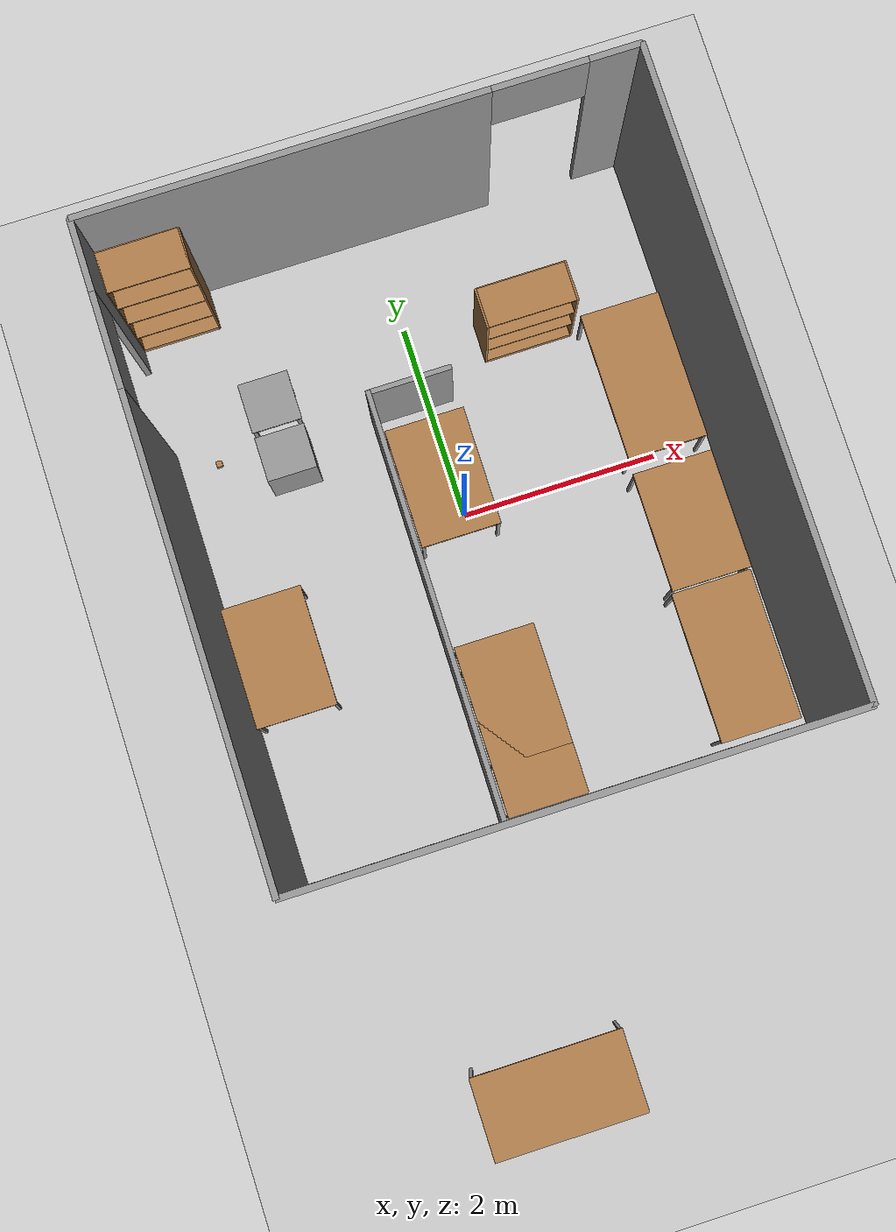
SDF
<?xml version="1.0" ?>
<sdf version="1.6">
  <world name="default">
    <light name="sun" type="directional">
      <cast_shadows>1</cast_shadows>
      <pose>0 0 10 0 -0 0</pose>
      <diffuse>0.8 0.8 0.8 1</diffuse>
      <specular>0.2 0.2 0.2 1</specular>
      <attenuation>
        <range>1000</range>
        <constant>0.9</constant>
        <linear>0.01</linear>
        <quadratic>0.001</quadratic>
      </attenuation>
      <direction>-0.5 0.1 -0.9</direction>
      <spot>
        <inner_angle>0</inner_angle>
        <outer_angle>0</outer_angle>
        <falloff>0</falloff>
      </spot>
    </light>
    <model name="ground_plane">
      <static>1</static>
      <link name="link">
        <collision name="collision">
          <geometry>
            <plane>
              <normal>0 0 1</normal>
              <size>100 100</size>
            </plane>
          </geometry>
          <surface>
            <contact>
              <collide_bitmask>65535</collide_bitmask>
              <ode/>
            </contact>
            <friction>
              <ode>
                <mu>100</mu>
                <mu2>50</mu2>
              </ode>
              <torsional>
                <ode/>
              </torsional>
            </friction>
            <bounce/>
          </surface>
          <max_contacts>10</max_contacts>
        </collision>
        <visual name="visual">
          <cast_shadows>0</cast_shadows>
          <geometry>
            <plane>
              <normal>0 0 1</normal>
              <size>100 100</size>
            </plane>
          </geometry>
          <material>
            <script>
              <uri>file://media/materials/scripts/gazebo.material</uri>
              <name>Gazebo/Grey</name>
            </script>
          </material>
        </visual>
        <self_collide>0</self_collide>
        <enable_wind>0</enable_wind>
        <kinematic>0</kinematic>
      </link>
    </model>
    <gravity>0 0 -9.8</gravity>
    <magnetic_field>6e-06 2.3e-05 -4.2e-05</magnetic_field>
    <atmosphere type="adiabatic"/>
    <physics type="ode">
      <max_step_size>0.001</max_step_size>
      <real_time_factor>1</real_time_factor>
      <real_time_update_rate>1000</real_time_update_rate>
    </physics>
    <scene>
      <ambient>0.4 0.4 0.4 1</ambient>
      <background>0.7 0.7 0.7 1</background>
      <shadows>1</shadows>
    </scene>
    <wind/>
    <spherical_coordinates>
      <surface_model>EARTH_WGS84</surface_model>
      <latitude_deg>0</latitude_deg>
      <longitude_deg>0</longitude_deg>
      <elevation>0</elevation>
      <heading_deg>0</heading_deg>
    </spherical_coordinates>
    <gui fullscreen="0">
      <camera name="user_camera">
        <pose>-0.54879 2.19319 3.95158 0 1.5618 -0.122154</pose>
        <view_controller>orbit</view_controller>
        <projection_type>perspective</projection_type>
      </camera>
    </gui>
    <model name="bookshelf_0">
      <static>1</static>
      <link name="link">
        <inertial>
          <mass>1</mass>
        </inertial>
        <collision name="back">
          <pose>0 0.005 0.6 0 -0 0</pose>
          <geometry>
            <box>
              <size>0.9 0.01 1.2</size>
            </box>
          </geometry>
          <max_contacts>10</max_contacts>
          <surface>
            <contact>
              <ode/>
            </contact>
            <bounce/>
            <friction>
              <torsional>
                <ode/>
              </torsional>
              <ode/>
            </friction>
          </surface>
        </collision>
        <visual name="visual1">
          <pose>0 0.005 0.6 0 -0 0</pose>
          <geometry>
            <box>
              <size>0.9 0.01 1.2</size>
            </box>
          </geometry>
          <material>
            <script>
              <uri>file://media/materials/scripts/gazebo.material</uri>
              <name>Gazebo/Wood</name>
            </script>
          </material>
        </visual>
        <collision name="left_side">
          <pose>0.45 -0.195 0.6 0 -0 0</pose>
          <geometry>
            <box>
              <size>0.02 0.4 1.2</size>
            </box>
          </geometry>
          <max_contacts>10</max_contacts>
          <surface>
            <contact>
              <ode/>
            </contact>
            <bounce/>
            <friction>
              <torsional>
                <ode/>
              </torsional>
              <ode/>
            </friction>
          </surface>
        </collision>
        <visual name="visual2">
          <pose>0.45 -0.195 0.6 0 -0 0</pose>
          <geometry>
            <box>
              <size>0.02 0.4 1.2</size>
            </box>
          </geometry>
          <material>
            <script>
              <uri>file://media/materials/scripts/gazebo.material</uri>
              <name>Gazebo/Wood</name>
            </script>
          </material>
        </visual>
        <collision name="right_side">
          <pose>-0.45 -0.195 0.6 0 -0 0</pose>
          <geometry>
            <box>
              <size>0.02 0.4 1.2</size>
            </box>
          </geometry>
          <max_contacts>10</max_contacts>
          <surface>
            <contact>
              <ode/>
            </contact>
            <bounce/>
            <friction>
              <torsional>
                <ode/>
              </torsional>
              <ode/>
            </friction>
          </surface>
        </collision>
        <visual name="visual3">
          <pose>-0.45 -0.195 0.6 0 -0 0</pose>
          <geometry>
            <box>
              <size>0.02 0.4 1.2</size>
            </box>
          </geometry>
          <material>
            <script>
              <uri>file://media/materials/scripts/gazebo.material</uri>
              <name>Gazebo/Wood</name>
            </script>
          </material>
        </visual>
        <collision name="bottom">
          <pose>0 -0.195 0.03 0 -0 0</pose>
          <geometry>
            <box>
              <size>0.88 0.4 0.06</size>
            </box>
          </geometry>
          <max_contacts>10</max_contacts>
          <surface>
            <contact>
              <ode/>
            </contact>
            <bounce/>
            <friction>
              <torsional>
                <ode/>
              </torsional>
              <ode/>
            </friction>
          </surface>
        </collision>
        <visual name="visual4">
          <pose>0 -0.195 0.03 0 -0 0</pose>
          <geometry>
            <box>
              <size>0.88 0.4 0.06</size>
            </box>
          </geometry>
          <material>
            <script>
              <uri>file://media/materials/scripts/gazebo.material</uri>
              <name>Gazebo/Wood</name>
            </script>
          </material>
        </visual>
        <collision name="top">
          <pose>0 -0.195 1.19 0 -0 0</pose>
          <geometry>
            <box>
              <size>0.88 0.4 0.02</size>
            </box>
          </geometry>
          <max_contacts>10</max_contacts>
          <surface>
            <contact>
              <ode/>
            </contact>
            <bounce/>
            <friction>
              <torsional>
                <ode/>
              </torsional>
              <ode/>
            </friction>
          </surface>
        </collision>
        <visual name="visual5">
          <pose>0 -0.195 1.19 0 -0 0</pose>
          <geometry>
            <box>
              <size>0.88 0.4 0.02</size>
            </box>
          </geometry>
          <material>
            <script>
              <uri>file://media/materials/scripts/gazebo.material</uri>
              <name>Gazebo/Wood</name>
            </script>
          </material>
        </visual>
        <collision name="low_shelf">
          <pose>0 -0.195 0.43 0 -0 0</pose>
          <geometry>
            <box>
              <size>0.88 0.4 0.02</size>
            </box>
          </geometry>
          <max_contacts>10</max_contacts>
          <surface>
            <contact>
              <ode/>
            </contact>
            <bounce/>
            <friction>
              <torsional>
                <ode/>
              </torsional>
              <ode/>
            </friction>
          </surface>
        </collision>
        <visual name="visual6">
          <pose>0 -0.195 0.43 0 -0 0</pose>
          <geometry>
            <box>
              <size>0.88 0.4 0.02</size>
            </box>
          </geometry>
          <material>
            <script>
              <uri>file://media/materials/scripts/gazebo.material</uri>
              <name>Gazebo/Wood</name>
            </script>
          </material>
        </visual>
        <collision name="high_shelf">
          <pose>0 -0.195 0.8 0 -0 0</pose>
          <geometry>
            <box>
              <size>0.88 0.4 0.02</size>
            </box>
          </geometry>
          <max_contacts>10</max_contacts>
          <surface>
            <contact>
              <ode/>
            </contact>
            <bounce/>
            <friction>
              <torsional>
                <ode/>
              </torsional>
              <ode/>
            </friction>
          </surface>
        </collision>
        <visual name="visual7">
          <pose>0 -0.195 0.8 0 -0 0</pose>
          <geometry>
            <box>
              <size>0.88 0.4 0.02</size>
            </box>
          </geometry>
          <material>
            <script>
              <uri>file://media/materials/scripts/gazebo.material</uri>
              <name>Gazebo/Wood</name>
            </script>
          </material>
        </visual>
        <self_collide>0</self_collide>
        <enable_wind>0</enable_wind>
        <kinematic>0</kinematic>
      </link>
      <pose>1.14304 1.83732 0 0 -0 0</pose>
    </model>
    <model name="IRAC">
      <link name="Wall_0">
        <pose>-2.61 0.007537 0 0 -0 1.5708</pose>
        <self_collide>0</self_collide>
        <enable_wind>0</enable_wind>
        <kinematic>0</kinematic>
        <gravity>1</gravity>
        <inertial>
          <mass>1</mass>
          <pose>0 0 0 0 -0 0</pose>
          <inertia>
            <ixx>1</ixx>
            <ixy>0</ixy>
            <ixz>0</ixz>
            <iyy>1</iyy>
            <iyz>0</iyz>
            <izz>1</izz>
          </inertia>
        </inertial>
        <visual name="Wall_0_Visual_0">
          <pose>-0.79786 0 1.35 0 -0 0</pose>
          <geometry>
            <box>
              <size>4.52428 0.06 2.7</size>
            </box>
          </geometry>
          <material>
            <script>
              <uri>file://media/materials/scripts/gazebo.material</uri>
              <name>Gazebo/Grey</name>
            </script>
            <ambient>1 1 1 1</ambient>
            <diffuse>0.7 0.7 0.7 1</diffuse>
            <specular>0.01 0.01 0.01 1</specular>
            <emissive>0 0 0 1</emissive>
          </material>
          <transparency>0</transparency>
          <cast_shadows>1</cast_shadows>
        </visual>
        <visual name="Wall_0_Visual_1">
          <pose>2.71214 0 1.35 0 -0 0</pose>
          <geometry>
            <box>
              <size>0.695721 0.06 2.7</size>
            </box>
          </geometry>
          <material>
            <script>
              <uri>file://media/materials/scripts/gazebo.material</uri>
              <name>Gazebo/Grey</name>
            </script>
            <ambient>1 1 1 1</ambient>
            <diffuse>0.7 0.7 0.7 1</diffuse>
            <specular>0.01 0.01 0.01 1</specular>
            <emissive>0 0 0 1</emissive>
          </material>
          <transparency>0</transparency>
          <cast_shadows>1</cast_shadows>
        </visual>
        <visual name="Wall_0_Visual_2">
          <pose>1.91428 0 2.35 0 -0 0</pose>
          <geometry>
            <box>
              <size>0.9 0.06 0.7</size>
            </box>
          </geometry>
          <material>
            <script>
              <uri>file://media/materials/scripts/gazebo.material</uri>
              <name>Gazebo/Grey</name>
            </script>
            <ambient>1 1 1 1</ambient>
            <diffuse>0.7 0.7 0.7 1</diffuse>
            <specular>0.01 0.01 0.01 1</specular>
            <emissive>0 0 0 1</emissive>
          </material>
          <transparency>0</transparency>
          <cast_shadows>1</cast_shadows>
        </visual>
        <collision name="Wall_0_Collision_0">
          <laser_retro>0</laser_retro>
          <max_contacts>10</max_contacts>
          <pose>-0.79786 0 1.35 0 -0 0</pose>
          <geometry>
            <box>
              <size>4.52428 0.06 2.7</size>
            </box>
          </geometry>
          <surface>
            <friction>
              <ode>
                <mu>1</mu>
                <mu2>1</mu2>
                <fdir1>0 0 0</fdir1>
                <slip1>0</slip1>
                <slip2>0</slip2>
              </ode>
              <torsional>
                <coefficient>1</coefficient>
                <patch_radius>0</patch_radius>
                <surface_radius>0</surface_radius>
                <use_patch_radius>1</use_patch_radius>
                <ode>
                  <slip>0</slip>
                </ode>
              </torsional>
            </friction>
            <bounce>
              <restitution_coefficient>0</restitution_coefficient>
              <threshold>1e+06</threshold>
            </bounce>
            <contact>
              <collide_without_contact>0</collide_without_contact>
              <collide_without_contact_bitmask>1</collide_without_contact_bitmask>
              <collide_bitmask>1</collide_bitmask>
              <ode>
                <soft_cfm>0</soft_cfm>
                <soft_erp>0.2</soft_erp>
                <kp>1e+13</kp>
                <kd>1</kd>
                <max_vel>0.01</max_vel>
                <min_depth>0</min_depth>
              </ode>
            </contact>
          </surface>
        </collision>
        <collision name="Wall_0_Collision_2">
          <laser_retro>0</laser_retro>
          <max_contacts>10</max_contacts>
          <pose>1.91428 0 2.35 0 -0 0</pose>
          <geometry>
            <box>
              <size>0.9 0.06 0.7</size>
            </box>
          </geometry>
          <surface>
            <friction>
              <ode>
                <mu>1</mu>
                <mu2>1</mu2>
                <fdir1>0 0 0</fdir1>
                <slip1>0</slip1>
                <slip2>0</slip2>
              </ode>
              <torsional>
                <coefficient>1</coefficient>
                <patch_radius>0</patch_radius>
                <surface_radius>0</surface_radius>
                <use_patch_radius>1</use_patch_radius>
                <ode>
                  <slip>0</slip>
                </ode>
              </torsional>
            </friction>
            <bounce>
              <restitution_coefficient>0</restitution_coefficient>
              <threshold>1e+06</threshold>
            </bounce>
            <contact>
              <collide_without_contact>0</collide_without_contact>
              <collide_without_contact_bitmask>1</collide_without_contact_bitmask>
              <collide_bitmask>1</collide_bitmask>
              <ode>
                <soft_cfm>0</soft_cfm>
                <soft_erp>0.2</soft_erp>
                <kp>1e+13</kp>
                <kd>1</kd>
                <max_vel>0.01</max_vel>
                <min_depth>0</min_depth>
              </ode>
            </contact>
          </surface>
        </collision>
        <collision name="Wall_0_Collision_1">
          <laser_retro>0</laser_retro>
          <max_contacts>10</max_contacts>
          <pose>2.71214 0 1.35 0 -0 0</pose>
          <geometry>
            <box>
              <size>0.695721 0.06 2.7</size>
            </box>
          </geometry>
          <surface>
            <friction>
              <ode>
                <mu>1</mu>
                <mu2>1</mu2>
                <fdir1>0 0 0</fdir1>
                <slip1>0</slip1>
                <slip2>0</slip2>
              </ode>
              <torsional>
                <coefficient>1</coefficient>
                <patch_radius>0</patch_radius>
                <surface_radius>0</surface_radius>
                <use_patch_radius>1</use_patch_radius>
                <ode>
                  <slip>0</slip>
                </ode>
              </torsional>
            </friction>
            <bounce>
              <restitution_coefficient>0</restitution_coefficient>
              <threshold>1e+06</threshold>
            </bounce>
            <contact>
              <collide_without_contact>0</collide_without_contact>
              <collide_without_contact_bitmask>1</collide_without_contact_bitmask>
              <collide_bitmask>1</collide_bitmask>
              <ode>
                <soft_cfm>0</soft_cfm>
                <soft_erp>0.2</soft_erp>
                <kp>1e+13</kp>
                <kd>1</kd>
                <max_vel>0.01</max_vel>
                <min_depth>0</min_depth>
              </ode>
            </contact>
          </surface>
        </collision>
      </link>
      <link name="Wall_11">
        <pose>-0.5825 -0.922463 0 0 -0 1.56726</pose>
        <self_collide>0</self_collide>
        <enable_wind>0</enable_wind>
        <kinematic>0</kinematic>
        <visual name="Wall_11_Visual">
          <pose>0 0 0.6 0 -0 0</pose>
          <geometry>
            <box>
              <size>4.29 0.05 1.2</size>
            </box>
          </geometry>
          <material>
            <script>
              <uri>file://media/materials/scripts/gazebo.material</uri>
              <name>Gazebo/Grey</name>
            </script>
            <ambient>1 1 1 1</ambient>
          </material>
          <transparency>0</transparency>
          <cast_shadows>1</cast_shadows>
        </visual>
        <collision name="Wall_11_Collision">
          <laser_retro>0</laser_retro>
          <max_contacts>10</max_contacts>
          <pose>0 0 0.6 0 -0 0</pose>
          <geometry>
            <box>
              <size>4.29 0.05 1.2</size>
            </box>
          </geometry>
          <surface>
            <friction>
              <ode>
                <mu>1</mu>
                <mu2>1</mu2>
                <fdir1>0 0 0</fdir1>
                <slip1>0</slip1>
                <slip2>0</slip2>
              </ode>
              <torsional>
                <coefficient>1</coefficient>
                <patch_radius>0</patch_radius>
                <surface_radius>0</surface_radius>
                <use_patch_radius>1</use_patch_radius>
                <ode>
                  <slip>0</slip>
                </ode>
              </torsional>
            </friction>
            <bounce>
              <restitution_coefficient>0</restitution_coefficient>
              <threshold>1e+06</threshold>
            </bounce>
            <contact>
              <collide_without_contact>0</collide_without_contact>
              <collide_without_contact_bitmask>1</collide_without_contact_bitmask>
              <collide_bitmask>1</collide_bitmask>
              <ode>
                <soft_cfm>0</soft_cfm>
                <soft_erp>0.2</soft_erp>
                <kp>1e+13</kp>
                <kd>1</kd>
                <max_vel>0.01</max_vel>
                <min_depth>0</min_depth>
              </ode>
            </contact>
          </surface>
        </collision>
      </link>
      <link name="Wall_13">
        <pose>-0.175 1.19754 0 0 -0 0</pose>
        <self_collide>0</self_collide>
        <enable_wind>0</enable_wind>
        <kinematic>0</kinematic>
        <visual name="Wall_13_Visual">
          <pose>0 0 0.6 0 -0 0</pose>
          <geometry>
            <box>
              <size>0.85 0.05 1.2</size>
            </box>
          </geometry>
          <material>
            <script>
              <uri>file://media/materials/scripts/gazebo.material</uri>
              <name>Gazebo/Grey</name>
            </script>
            <ambient>1 1 1 1</ambient>
          </material>
          <transparency>0</transparency>
          <cast_shadows>1</cast_shadows>
        </visual>
        <collision name="Wall_13_Collision">
          <laser_retro>0</laser_retro>
          <max_contacts>10</max_contacts>
          <pose>0 0 0.6 0 -0 0</pose>
          <geometry>
            <box>
              <size>0.85 0.05 1.2</size>
            </box>
          </geometry>
          <surface>
            <friction>
              <ode>
                <mu>1</mu>
                <mu2>1</mu2>
                <fdir1>0 0 0</fdir1>
                <slip1>0</slip1>
                <slip2>0</slip2>
              </ode>
              <torsional>
                <coefficient>1</coefficient>
                <patch_radius>0</patch_radius>
                <surface_radius>0</surface_radius>
                <use_patch_radius>1</use_patch_radius>
                <ode>
                  <slip>0</slip>
                </ode>
              </torsional>
            </friction>
            <bounce>
              <restitution_coefficient>0</restitution_coefficient>
              <threshold>1e+06</threshold>
            </bounce>
            <contact>
              <collide_without_contact>0</collide_without_contact>
              <collide_without_contact_bitmask>1</collide_without_contact_bitmask>
              <collide_bitmask>1</collide_bitmask>
              <ode>
                <soft_cfm>0</soft_cfm>
                <soft_erp>0.2</soft_erp>
                <kp>1e+13</kp>
                <kd>1</kd>
                <max_vel>0.01</max_vel>
                <min_depth>0</min_depth>
              </ode>
            </contact>
          </surface>
        </collision>
      </link>
      <link name="Wall_2">
        <pose>0 -3.04246 0 0 -0 0</pose>
        <self_collide>0</self_collide>
        <enable_wind>0</enable_wind>
        <kinematic>0</kinematic>
        <gravity>1</gravity>
        <inertial>
          <mass>1</mass>
          <pose>0 0 0 0 -0 0</pose>
          <inertia>
            <ixx>1</ixx>
            <ixy>0</ixy>
            <ixz>0</ixz>
            <iyy>1</iyy>
            <iyz>0</iyz>
            <izz>1</izz>
          </inertia>
        </inertial>
        <visual name="Wall_2_Visual">
          <pose>0 0 1.35 0 -0 0</pose>
          <geometry>
            <box>
              <size>5.24 0.06 2.7</size>
            </box>
          </geometry>
          <material>
            <script>
              <uri>file://media/materials/scripts/gazebo.material</uri>
              <name>Gazebo/Grey</name>
            </script>
            <ambient>1 1 1 1</ambient>
            <diffuse>0.7 0.7 0.7 1</diffuse>
            <specular>0.01 0.01 0.01 1</specular>
            <emissive>0 0 0 1</emissive>
          </material>
          <transparency>0</transparency>
          <cast_shadows>1</cast_shadows>
        </visual>
        <collision name="Wall_2_Collision">
          <laser_retro>0</laser_retro>
          <max_contacts>10</max_contacts>
          <pose>0 0 1.35 0 -0 0</pose>
          <geometry>
            <box>
              <size>5.24 0.06 2.7</size>
            </box>
          </geometry>
          <surface>
            <friction>
              <ode>
                <mu>1</mu>
                <mu2>1</mu2>
                <fdir1>0 0 0</fdir1>
                <slip1>0</slip1>
                <slip2>0</slip2>
              </ode>
              <torsional>
                <coefficient>1</coefficient>
                <patch_radius>0</patch_radius>
                <surface_radius>0</surface_radius>
                <use_patch_radius>1</use_patch_radius>
                <ode>
                  <slip>0</slip>
                </ode>
              </torsional>
            </friction>
            <bounce>
              <restitution_coefficient>0</restitution_coefficient>
              <threshold>1e+06</threshold>
            </bounce>
            <contact>
              <collide_without_contact>0</collide_without_contact>
              <collide_without_contact_bitmask>1</collide_without_contact_bitmask>
              <collide_bitmask>1</collide_bitmask>
              <ode>
                <soft_cfm>0</soft_cfm>
                <soft_erp>0.2</soft_erp>
                <kp>1e+13</kp>
                <kd>1</kd>
                <max_vel>0.01</max_vel>
                <min_depth>0</min_depth>
              </ode>
            </contact>
          </surface>
        </collision>
      </link>
      <link name="Wall_4">
        <pose>2.61 0.007537 0 0 -0 1.5708</pose>
        <self_collide>0</self_collide>
        <enable_wind>0</enable_wind>
        <kinematic>0</kinematic>
        <gravity>1</gravity>
        <inertial>
          <mass>1</mass>
          <pose>0 0 0 0 -0 0</pose>
          <inertia>
            <ixx>1</ixx>
            <ixy>0</ixy>
            <ixz>0</ixz>
            <iyy>1</iyy>
            <iyz>0</iyz>
            <izz>1</izz>
          </inertia>
        </inertial>
        <visual name="Wall_4_Visual">
          <pose>0 0 1.35 0 -0 0</pose>
          <geometry>
            <box>
              <size>6.12 0.06 2.7</size>
            </box>
          </geometry>
          <material>
            <script>
              <uri>file://media/materials/scripts/gazebo.material</uri>
              <name>Gazebo/Grey</name>
            </script>
            <ambient>1 1 1 1</ambient>
            <diffuse>0.7 0.7 0.7 1</diffuse>
            <specular>0.01 0.01 0.01 1</specular>
            <emissive>0 0 0 1</emissive>
          </material>
          <transparency>0</transparency>
          <cast_shadows>1</cast_shadows>
        </visual>
        <collision name="Wall_4_Collision">
          <laser_retro>0</laser_retro>
          <max_contacts>10</max_contacts>
          <pose>0 0 1.35 0 -0 0</pose>
          <geometry>
            <box>
              <size>6.12 0.06 2.7</size>
            </box>
          </geometry>
          <surface>
            <friction>
              <ode>
                <mu>1</mu>
                <mu2>1</mu2>
                <fdir1>0 0 0</fdir1>
                <slip1>0</slip1>
                <slip2>0</slip2>
              </ode>
              <torsional>
                <coefficient>1</coefficient>
                <patch_radius>0</patch_radius>
                <surface_radius>0</surface_radius>
                <use_patch_radius>1</use_patch_radius>
                <ode>
                  <slip>0</slip>
                </ode>
              </torsional>
            </friction>
            <bounce>
              <restitution_coefficient>0</restitution_coefficient>
              <threshold>1e+06</threshold>
            </bounce>
            <contact>
              <collide_without_contact>0</collide_without_contact>
              <collide_without_contact_bitmask>1</collide_without_contact_bitmask>
              <collide_bitmask>1</collide_bitmask>
              <ode>
                <soft_cfm>0</soft_cfm>
                <soft_erp>0.2</soft_erp>
                <kp>1e+13</kp>
                <kd>1</kd>
                <max_vel>0.01</max_vel>
                <min_depth>0</min_depth>
              </ode>
            </contact>
          </surface>
        </collision>
      </link>
      <link name="Wall_9">
        <pose>0 3.05754 0 0 -0 0</pose>
        <self_collide>0</self_collide>
        <enable_wind>0</enable_wind>
        <kinematic>0</kinematic>
        <gravity>1</gravity>
        <inertial>
          <mass>1</mass>
          <pose>0 0 0 0 -0 0</pose>
          <inertia>
            <ixx>1</ixx>
            <ixy>0</ixy>
            <ixz>0</ixz>
            <iyy>1</iyy>
            <iyz>0</iyz>
            <izz>1</izz>
          </inertia>
        </inertial>
        <visual name="Wall_9_Visual_0">
          <pose>-0.699649 0 1.35 0 -0 0</pose>
          <geometry>
            <box>
              <size>3.8407 0.06 2.7</size>
            </box>
          </geometry>
          <material>
            <script>
              <uri>file://media/materials/scripts/gazebo.material</uri>
              <name>Gazebo/Grey</name>
            </script>
            <ambient>1 1 1 1</ambient>
            <diffuse>0.7 0.7 0.7 1</diffuse>
            <specular>0.01 0.01 0.01 1</specular>
            <emissive>0 0 0 1</emissive>
          </material>
          <transparency>0</transparency>
          <cast_shadows>1</cast_shadows>
        </visual>
        <visual name="Wall_9_Visual_1">
          <pose>2.37035 0 1.35 0 -0 0</pose>
          <geometry>
            <box>
              <size>0.499297 0.06 2.7</size>
            </box>
          </geometry>
          <material>
            <script>
              <uri>file://media/materials/scripts/gazebo.material</uri>
              <name>Gazebo/Grey</name>
            </script>
            <ambient>1 1 1 1</ambient>
            <diffuse>0.7 0.7 0.7 1</diffuse>
            <specular>0.01 0.01 0.01 1</specular>
            <emissive>0 0 0 1</emissive>
          </material>
          <transparency>0</transparency>
          <cast_shadows>1</cast_shadows>
        </visual>
        <visual name="Wall_9_Visual_2">
          <pose>1.6707 0 2.35 0 -0 0</pose>
          <geometry>
            <box>
              <size>0.9 0.06 0.7</size>
            </box>
          </geometry>
          <material>
            <script>
              <uri>file://media/materials/scripts/gazebo.material</uri>
              <name>Gazebo/Grey</name>
            </script>
            <ambient>1 1 1 1</ambient>
            <diffuse>0.7 0.7 0.7 1</diffuse>
            <specular>0.01 0.01 0.01 1</specular>
            <emissive>0 0 0 1</emissive>
          </material>
          <transparency>0</transparency>
          <cast_shadows>1</cast_shadows>
        </visual>
        <collision name="Wall_9_Collision_0">
          <laser_retro>0</laser_retro>
          <max_contacts>10</max_contacts>
          <pose>-0.699649 0 1.35 0 -0 0</pose>
          <geometry>
            <box>
              <size>3.8407 0.06 2.7</size>
            </box>
          </geometry>
          <surface>
            <friction>
              <ode>
                <mu>1</mu>
                <mu2>1</mu2>
                <fdir1>0 0 0</fdir1>
                <slip1>0</slip1>
                <slip2>0</slip2>
              </ode>
              <torsional>
                <coefficient>1</coefficient>
                <patch_radius>0</patch_radius>
                <surface_radius>0</surface_radius>
                <use_patch_radius>1</use_patch_radius>
                <ode>
                  <slip>0</slip>
                </ode>
              </torsional>
            </friction>
            <bounce>
              <restitution_coefficient>0</restitution_coefficient>
              <threshold>1e+06</threshold>
            </bounce>
            <contact>
              <collide_without_contact>0</collide_without_contact>
              <collide_without_contact_bitmask>1</collide_without_contact_bitmask>
              <collide_bitmask>1</collide_bitmask>
              <ode>
                <soft_cfm>0</soft_cfm>
                <soft_erp>0.2</soft_erp>
                <kp>1e+13</kp>
                <kd>1</kd>
                <max_vel>0.01</max_vel>
                <min_depth>0</min_depth>
              </ode>
            </contact>
          </surface>
        </collision>
        <collision name="Wall_9_Collision_1">
          <laser_retro>0</laser_retro>
          <max_contacts>10</max_contacts>
          <pose>2.37035 0 1.35 0 -0 0</pose>
          <geometry>
            <box>
              <size>0.499297 0.06 2.7</size>
            </box>
          </geometry>
          <surface>
            <friction>
              <ode>
                <mu>1</mu>
                <mu2>1</mu2>
                <fdir1>0 0 0</fdir1>
                <slip1>0</slip1>
                <slip2>0</slip2>
              </ode>
              <torsional>
                <coefficient>1</coefficient>
                <patch_radius>0</patch_radius>
                <surface_radius>0</surface_radius>
                <use_patch_radius>1</use_patch_radius>
                <ode>
                  <slip>0</slip>
                </ode>
              </torsional>
            </friction>
            <bounce>
              <restitution_coefficient>0</restitution_coefficient>
              <threshold>1e+06</threshold>
            </bounce>
            <contact>
              <collide_without_contact>0</collide_without_contact>
              <collide_without_contact_bitmask>1</collide_without_contact_bitmask>
              <collide_bitmask>1</collide_bitmask>
              <ode>
                <soft_cfm>0</soft_cfm>
                <soft_erp>0.2</soft_erp>
                <kp>1e+13</kp>
                <kd>1</kd>
                <max_vel>0.01</max_vel>
                <min_depth>0</min_depth>
              </ode>
            </contact>
          </surface>
        </collision>
        <collision name="Wall_9_Collision_2">
          <laser_retro>0</laser_retro>
          <max_contacts>10</max_contacts>
          <pose>1.6707 0 2.35 0 -0 0</pose>
          <geometry>
            <box>
              <size>0.9 0.06 0.7</size>
            </box>
          </geometry>
          <surface>
            <friction>
              <ode>
                <mu>1</mu>
                <mu2>1</mu2>
                <fdir1>0 0 0</fdir1>
                <slip1>0</slip1>
                <slip2>0</slip2>
              </ode>
              <torsional>
                <coefficient>1</coefficient>
                <patch_radius>0</patch_radius>
                <surface_radius>0</surface_radius>
                <use_patch_radius>1</use_patch_radius>
                <ode>
                  <slip>0</slip>
                </ode>
              </torsional>
            </friction>
            <bounce>
              <restitution_coefficient>0</restitution_coefficient>
              <threshold>1e+06</threshold>
            </bounce>
            <contact>
              <collide_without_contact>0</collide_without_contact>
              <collide_without_contact_bitmask>1</collide_without_contact_bitmask>
              <collide_bitmask>1</collide_bitmask>
              <ode>
                <soft_cfm>0</soft_cfm>
                <soft_erp>0.2</soft_erp>
                <kp>1e+13</kp>
                <kd>1</kd>
                <max_vel>0.01</max_vel>
                <min_depth>0</min_depth>
              </ode>
            </contact>
          </surface>
        </collision>
      </link>
      <static>1</static>
      <pose>0 -0.007537 0 0 -0 0</pose>
    </model>
    <model name="table_long">
      <link name="link">
        <self_collide>0</self_collide>
        <enable_wind>0</enable_wind>
        <kinematic>0</kinematic>
        <pose>0 0 0 0 -0 0</pose>
        <gravity>1</gravity>
        <inertial>
          <mass>1</mass>
          <pose>0 0 0 0 -0 0</pose>
          <inertia>
            <ixx>1</ixx>
            <ixy>0</ixy>
            <ixz>0</ixz>
            <iyy>1</iyy>
            <iyz>0</iyz>
            <izz>1</izz>
          </inertia>
        </inertial>
        <visual name="front_left_leg">
          <pose>0.73 0.38 0.35 0 -0 0</pose>
          <geometry>
            <box>
              <size>0.03 0.03 0.7</size>
            </box>
          </geometry>
          <material>
            <script>
              <uri>file://media/materials/scripts/gazebo.material</uri>
              <name>Gazebo/Grey</name>
            </script>
            <ambient>0.3 0.3 0.3 1</ambient>
            <diffuse>0.7 0.7 0.7 1</diffuse>
            <specular>0.01 0.01 0.01 1</specular>
            <emissive>0 0 0 1</emissive>
          </material>
          <transparency>0</transparency>
          <cast_shadows>1</cast_shadows>
        </visual>
        <visual name="front_right_leg">
          <pose>0.73 -0.38 0.35 0 -0 0</pose>
          <geometry>
            <box>
              <size>0.03 0.03 0.7</size>
            </box>
          </geometry>
          <material>
            <script>
              <uri>file://media/materials/scripts/gazebo.material</uri>
              <name>Gazebo/Grey</name>
            </script>
            <ambient>0.3 0.3 0.3 1</ambient>
            <diffuse>0.7 0.7 0.7 1</diffuse>
            <specular>0.01 0.01 0.01 1</specular>
            <emissive>0 0 0 1</emissive>
          </material>
          <transparency>0</transparency>
          <cast_shadows>1</cast_shadows>
        </visual>
        <visual name="visual1">
          <pose>0 0 0.7 0 -0 0</pose>
          <geometry>
            <box>
              <size>1.5 0.8 0.04</size>
            </box>
          </geometry>
          <material>
            <script>
              <uri>file://media/materials/scripts/gazebo.material</uri>
              <name>Gazebo/Wood</name>
            </script>
            <ambient>1 1 1 1</ambient>
            <diffuse>1 1 1 1</diffuse>
            <specular>0.2 0.2 0.2 1</specular>
            <emissive>0 0 0 1</emissive>
          </material>
          <transparency>0</transparency>
          <cast_shadows>1</cast_shadows>
        </visual>
        <visual name="back_right_leg">
          <pose>-0.73 -0.38 0.35 0 -0 0</pose>
          <geometry>
            <box>
              <size>0.03 0.03 0.7</size>
            </box>
          </geometry>
          <material>
            <script>
              <uri>file://media/materials/scripts/gazebo.material</uri>
              <name>Gazebo/Grey</name>
            </script>
            <ambient>0.3 0.3 0.3 1</ambient>
            <diffuse>0.7 0.7 0.7 1</diffuse>
            <specular>0.01 0.01 0.01 1</specular>
            <emissive>0 0 0 1</emissive>
          </material>
          <transparency>0</transparency>
          <cast_shadows>1</cast_shadows>
        </visual>
        <visual name="back_left_leg">
          <pose>-0.73 0.38 0.35 0 -0 0</pose>
          <geometry>
            <box>
              <size>0.03 0.03 0.7</size>
            </box>
          </geometry>
          <material>
            <script>
              <uri>file://media/materials/scripts/gazebo.material</uri>
              <name>Gazebo/Grey</name>
            </script>
            <ambient>0.3 0.3 0.3 1</ambient>
            <diffuse>0.7 0.7 0.7 1</diffuse>
            <specular>0.01 0.01 0.01 1</specular>
            <emissive>0 0 0 1</emissive>
          </material>
          <transparency>0</transparency>
          <cast_shadows>1</cast_shadows>
        </visual>
        <collision name="front_right_leg">
          <laser_retro>0</laser_retro>
          <max_contacts>10</max_contacts>
          <pose>0.73 -0.38 0.35 0 -0 0</pose>
          <geometry>
            <box>
              <size>0.03 0.03 0.7</size>
            </box>
          </geometry>
          <surface>
            <friction>
              <ode>
                <mu>1</mu>
                <mu2>1</mu2>
                <fdir1>0 0 0</fdir1>
                <slip1>0</slip1>
                <slip2>0</slip2>
              </ode>
              <torsional>
                <coefficient>1</coefficient>
                <patch_radius>0</patch_radius>
                <surface_radius>0</surface_radius>
                <use_patch_radius>1</use_patch_radius>
                <ode>
                  <slip>0</slip>
                </ode>
              </torsional>
            </friction>
            <bounce>
              <restitution_coefficient>0</restitution_coefficient>
              <threshold>1e+06</threshold>
            </bounce>
            <contact>
              <collide_without_contact>0</collide_without_contact>
              <collide_without_contact_bitmask>1</collide_without_contact_bitmask>
              <collide_bitmask>1</collide_bitmask>
              <ode>
                <soft_cfm>0</soft_cfm>
                <soft_erp>0.2</soft_erp>
                <kp>1e+13</kp>
                <kd>1</kd>
                <max_vel>0.01</max_vel>
                <min_depth>0</min_depth>
              </ode>
            </contact>
          </surface>
        </collision>
        <collision name="front_left_leg">
          <laser_retro>0</laser_retro>
          <max_contacts>10</max_contacts>
          <pose>0.73 0.38 0.35 0 -0 0</pose>
          <geometry>
            <box>
              <size>0.03 0.03 0.699999</size>
            </box>
          </geometry>
          <surface>
            <friction>
              <ode>
                <mu>1</mu>
                <mu2>1</mu2>
                <fdir1>0 0 0</fdir1>
                <slip1>0</slip1>
                <slip2>0</slip2>
              </ode>
              <torsional>
                <coefficient>1</coefficient>
                <patch_radius>0</patch_radius>
                <surface_radius>0</surface_radius>
                <use_patch_radius>1</use_patch_radius>
                <ode>
                  <slip>0</slip>
                </ode>
              </torsional>
            </friction>
            <bounce>
              <restitution_coefficient>0</restitution_coefficient>
              <threshold>1e+06</threshold>
            </bounce>
            <contact>
              <collide_without_contact>0</collide_without_contact>
              <collide_without_contact_bitmask>1</collide_without_contact_bitmask>
              <collide_bitmask>1</collide_bitmask>
              <ode>
                <soft_cfm>0</soft_cfm>
                <soft_erp>0.2</soft_erp>
                <kp>1e+13</kp>
                <kd>1</kd>
                <max_vel>0.01</max_vel>
                <min_depth>0</min_depth>
              </ode>
            </contact>
          </surface>
        </collision>
        <collision name="back_right_leg">
          <laser_retro>0</laser_retro>
          <max_contacts>10</max_contacts>
          <pose>-0.73 -0.38 0.35 0 -0 0</pose>
          <geometry>
            <box>
              <size>0.03 0.03 0.7</size>
            </box>
          </geometry>
          <surface>
            <friction>
              <ode>
                <mu>1</mu>
                <mu2>1</mu2>
                <fdir1>0 0 0</fdir1>
                <slip1>0</slip1>
                <slip2>0</slip2>
              </ode>
              <torsional>
                <coefficient>1</coefficient>
                <patch_radius>0</patch_radius>
                <surface_radius>0</surface_radius>
                <use_patch_radius>1</use_patch_radius>
                <ode>
                  <slip>0</slip>
                </ode>
              </torsional>
            </friction>
            <bounce>
              <restitution_coefficient>0</restitution_coefficient>
              <threshold>1e+06</threshold>
            </bounce>
            <contact>
              <collide_without_contact>0</collide_without_contact>
              <collide_without_contact_bitmask>1</collide_without_contact_bitmask>
              <collide_bitmask>1</collide_bitmask>
              <ode>
                <soft_cfm>0</soft_cfm>
                <soft_erp>0.2</soft_erp>
                <kp>1e+13</kp>
                <kd>1</kd>
                <max_vel>0.01</max_vel>
                <min_depth>0</min_depth>
              </ode>
            </contact>
          </surface>
        </collision>
        <collision name="surface">
          <laser_retro>0</laser_retro>
          <max_contacts>10</max_contacts>
          <pose>0 0 0.7 0 -0 0</pose>
          <geometry>
            <box>
              <size>1.5 0.8 0.04</size>
            </box>
          </geometry>
          <surface>
            <friction>
              <ode>
                <mu>0.6</mu>
                <mu2>0.6</mu2>
                <fdir1>0 0 0</fdir1>
                <slip1>0</slip1>
                <slip2>0</slip2>
              </ode>
              <torsional>
                <coefficient>1</coefficient>
                <patch_radius>0</patch_radius>
                <surface_radius>0</surface_radius>
                <use_patch_radius>1</use_patch_radius>
                <ode>
                  <slip>0</slip>
                </ode>
              </torsional>
            </friction>
            <bounce>
              <restitution_coefficient>0</restitution_coefficient>
              <threshold>1e+06</threshold>
            </bounce>
            <contact>
              <collide_without_contact>0</collide_without_contact>
              <collide_without_contact_bitmask>1</collide_without_contact_bitmask>
              <collide_bitmask>1</collide_bitmask>
              <ode>
                <soft_cfm>0</soft_cfm>
                <soft_erp>0.2</soft_erp>
                <kp>1e+13</kp>
                <kd>1</kd>
                <max_vel>0.01</max_vel>
                <min_depth>0</min_depth>
              </ode>
            </contact>
          </surface>
        </collision>
        <collision name="back_left_leg">
          <laser_retro>0</laser_retro>
          <max_contacts>10</max_contacts>
          <pose>-0.73 0.38 0.35 0 -0 0</pose>
          <geometry>
            <box>
              <size>0.03 0.03 0.7</size>
            </box>
          </geometry>
          <surface>
            <friction>
              <ode>
                <mu>1</mu>
                <mu2>1</mu2>
                <fdir1>0 0 0</fdir1>
                <slip1>0</slip1>
                <slip2>0</slip2>
              </ode>
              <torsional>
                <coefficient>1</coefficient>
                <patch_radius>0</patch_radius>
                <surface_radius>0</surface_radius>
                <use_patch_radius>1</use_patch_radius>
                <ode>
                  <slip>0</slip>
                </ode>
              </torsional>
            </friction>
            <bounce>
              <restitution_coefficient>0</restitution_coefficient>
              <threshold>1e+06</threshold>
            </bounce>
            <contact>
              <collide_without_contact>0</collide_without_contact>
              <collide_without_contact_bitmask>1</collide_without_contact_bitmask>
              <collide_bitmask>1</collide_bitmask>
              <ode>
                <soft_cfm>0</soft_cfm>
                <soft_erp>0.2</soft_erp>
                <kp>1e+13</kp>
                <kd>1</kd>
                <max_vel>0.01</max_vel>
                <min_depth>0</min_depth>
              </ode>
            </contact>
          </surface>
        </collision>
      </link>
      <static>1</static>
      <pose>-0.873749 -5.57004 0 0 -0 0</pose>
    </model>
    <model name="table_long_clone">
      <link name="link">
        <self_collide>0</self_collide>
        <enable_wind>0</enable_wind>
        <kinematic>0</kinematic>
        <pose>0 0 0 0 -0 0</pose>
        <gravity>1</gravity>
        <inertial>
          <mass>1</mass>
          <pose>0 0 0 0 -0 0</pose>
          <inertia>
            <ixx>1</ixx>
            <ixy>0</ixy>
            <ixz>0</ixz>
            <iyy>1</iyy>
            <iyz>0</iyz>
            <izz>1</izz>
          </inertia>
        </inertial>
        <visual name="front_left_leg">
          <pose>0.73 0.38 0.35 0 -0 0</pose>
          <geometry>
            <box>
              <size>0.03 0.03 0.7</size>
            </box>
          </geometry>
          <material>
            <script>
              <uri>file://media/materials/scripts/gazebo.material</uri>
              <name>Gazebo/Grey</name>
            </script>
            <ambient>0.3 0.3 0.3 1</ambient>
            <diffuse>0.7 0.7 0.7 1</diffuse>
            <specular>0.01 0.01 0.01 1</specular>
            <emissive>0 0 0 1</emissive>
          </material>
          <transparency>0</transparency>
          <cast_shadows>1</cast_shadows>
        </visual>
        <visual name="front_right_leg">
          <pose>0.73 -0.38 0.35 0 -0 0</pose>
          <geometry>
            <box>
              <size>0.03 0.03 0.7</size>
            </box>
          </geometry>
          <material>
            <script>
              <uri>file://media/materials/scripts/gazebo.material</uri>
              <name>Gazebo/Grey</name>
            </script>
            <ambient>0.3 0.3 0.3 1</ambient>
            <diffuse>0.7 0.7 0.7 1</diffuse>
            <specular>0.01 0.01 0.01 1</specular>
            <emissive>0 0 0 1</emissive>
          </material>
          <transparency>0</transparency>
          <cast_shadows>1</cast_shadows>
        </visual>
        <visual name="visual1">
          <pose>0 0 0.7 0 -0 0</pose>
          <geometry>
            <box>
              <size>1.5 0.8 0.04</size>
            </box>
          </geometry>
          <material>
            <script>
              <uri>file://media/materials/scripts/gazebo.material</uri>
              <name>Gazebo/Wood</name>
            </script>
            <ambient>1 1 1 1</ambient>
            <diffuse>1 1 1 1</diffuse>
            <specular>0.2 0.2 0.2 1</specular>
            <emissive>0 0 0 1</emissive>
          </material>
          <transparency>0</transparency>
          <cast_shadows>1</cast_shadows>
        </visual>
        <visual name="back_right_leg">
          <pose>-0.73 -0.38 0.35 0 -0 0</pose>
          <geometry>
            <box>
              <size>0.03 0.03 0.7</size>
            </box>
          </geometry>
          <material>
            <script>
              <uri>file://media/materials/scripts/gazebo.material</uri>
              <name>Gazebo/Grey</name>
            </script>
            <ambient>0.3 0.3 0.3 1</ambient>
            <diffuse>0.7 0.7 0.7 1</diffuse>
            <specular>0.01 0.01 0.01 1</specular>
            <emissive>0 0 0 1</emissive>
          </material>
          <transparency>0</transparency>
          <cast_shadows>1</cast_shadows>
        </visual>
        <visual name="back_left_leg">
          <pose>-0.73 0.38 0.35 0 -0 0</pose>
          <geometry>
            <box>
              <size>0.03 0.03 0.7</size>
            </box>
          </geometry>
          <material>
            <script>
              <uri>file://media/materials/scripts/gazebo.material</uri>
              <name>Gazebo/Grey</name>
            </script>
            <ambient>0.3 0.3 0.3 1</ambient>
            <diffuse>0.7 0.7 0.7 1</diffuse>
            <specular>0.01 0.01 0.01 1</specular>
            <emissive>0 0 0 1</emissive>
          </material>
          <transparency>0</transparency>
          <cast_shadows>1</cast_shadows>
        </visual>
        <collision name="front_right_leg">
          <laser_retro>0</laser_retro>
          <max_contacts>10</max_contacts>
          <pose>0.73 -0.38 0.35 0 -0 0</pose>
          <geometry>
            <box>
              <size>0.03 0.03 0.7</size>
            </box>
          </geometry>
          <surface>
            <friction>
              <ode>
                <mu>1</mu>
                <mu2>1</mu2>
                <fdir1>0 0 0</fdir1>
                <slip1>0</slip1>
                <slip2>0</slip2>
              </ode>
              <torsional>
                <coefficient>1</coefficient>
                <patch_radius>0</patch_radius>
                <surface_radius>0</surface_radius>
                <use_patch_radius>1</use_patch_radius>
                <ode>
                  <slip>0</slip>
                </ode>
              </torsional>
            </friction>
            <bounce>
              <restitution_coefficient>0</restitution_coefficient>
              <threshold>1e+06</threshold>
            </bounce>
            <contact>
              <collide_without_contact>0</collide_without_contact>
              <collide_without_contact_bitmask>1</collide_without_contact_bitmask>
              <collide_bitmask>1</collide_bitmask>
              <ode>
                <soft_cfm>0</soft_cfm>
                <soft_erp>0.2</soft_erp>
                <kp>1e+13</kp>
                <kd>1</kd>
                <max_vel>0.01</max_vel>
                <min_depth>0</min_depth>
              </ode>
            </contact>
          </surface>
        </collision>
        <collision name="front_left_leg">
          <laser_retro>0</laser_retro>
          <max_contacts>10</max_contacts>
          <pose>0.73 0.38 0.35 0 -0 0</pose>
          <geometry>
            <box>
              <size>0.03 0.03 0.699999</size>
            </box>
          </geometry>
          <surface>
            <friction>
              <ode>
                <mu>1</mu>
                <mu2>1</mu2>
                <fdir1>0 0 0</fdir1>
                <slip1>0</slip1>
                <slip2>0</slip2>
              </ode>
              <torsional>
                <coefficient>1</coefficient>
                <patch_radius>0</patch_radius>
                <surface_radius>0</surface_radius>
                <use_patch_radius>1</use_patch_radius>
                <ode>
                  <slip>0</slip>
                </ode>
              </torsional>
            </friction>
            <bounce>
              <restitution_coefficient>0</restitution_coefficient>
              <threshold>1e+06</threshold>
            </bounce>
            <contact>
              <collide_without_contact>0</collide_without_contact>
              <collide_without_contact_bitmask>1</collide_without_contact_bitmask>
              <collide_bitmask>1</collide_bitmask>
              <ode>
                <soft_cfm>0</soft_cfm>
                <soft_erp>0.2</soft_erp>
                <kp>1e+13</kp>
                <kd>1</kd>
                <max_vel>0.01</max_vel>
                <min_depth>0</min_depth>
              </ode>
            </contact>
          </surface>
        </collision>
        <collision name="back_right_leg">
          <laser_retro>0</laser_retro>
          <max_contacts>10</max_contacts>
          <pose>-0.73 -0.38 0.35 0 -0 0</pose>
          <geometry>
            <box>
              <size>0.03 0.03 0.7</size>
            </box>
          </geometry>
          <surface>
            <friction>
              <ode>
                <mu>1</mu>
                <mu2>1</mu2>
                <fdir1>0 0 0</fdir1>
                <slip1>0</slip1>
                <slip2>0</slip2>
              </ode>
              <torsional>
                <coefficient>1</coefficient>
                <patch_radius>0</patch_radius>
                <surface_radius>0</surface_radius>
                <use_patch_radius>1</use_patch_radius>
                <ode>
                  <slip>0</slip>
                </ode>
              </torsional>
            </friction>
            <bounce>
              <restitution_coefficient>0</restitution_coefficient>
              <threshold>1e+06</threshold>
            </bounce>
            <contact>
              <collide_without_contact>0</collide_without_contact>
              <collide_without_contact_bitmask>1</collide_without_contact_bitmask>
              <collide_bitmask>1</collide_bitmask>
              <ode>
                <soft_cfm>0</soft_cfm>
                <soft_erp>0.2</soft_erp>
                <kp>1e+13</kp>
                <kd>1</kd>
                <max_vel>0.01</max_vel>
                <min_depth>0</min_depth>
              </ode>
            </contact>
          </surface>
        </collision>
        <collision name="surface">
          <laser_retro>0</laser_retro>
          <max_contacts>10</max_contacts>
          <pose>0 0 0.7 0 -0 0</pose>
          <geometry>
            <box>
              <size>1.5 0.8 0.04</size>
            </box>
          </geometry>
          <surface>
            <friction>
              <ode>
                <mu>0.6</mu>
                <mu2>0.6</mu2>
                <fdir1>0 0 0</fdir1>
                <slip1>0</slip1>
                <slip2>0</slip2>
              </ode>
              <torsional>
                <coefficient>1</coefficient>
                <patch_radius>0</patch_radius>
                <surface_radius>0</surface_radius>
                <use_patch_radius>1</use_patch_radius>
                <ode>
                  <slip>0</slip>
                </ode>
              </torsional>
            </friction>
            <bounce>
              <restitution_coefficient>0</restitution_coefficient>
              <threshold>1e+06</threshold>
            </bounce>
            <contact>
              <collide_without_contact>0</collide_without_contact>
              <collide_without_contact_bitmask>1</collide_without_contact_bitmask>
              <collide_bitmask>1</collide_bitmask>
              <ode>
                <soft_cfm>0</soft_cfm>
                <soft_erp>0.2</soft_erp>
                <kp>1e+13</kp>
                <kd>1</kd>
                <max_vel>0.01</max_vel>
                <min_depth>0</min_depth>
              </ode>
            </contact>
          </surface>
        </collision>
        <collision name="back_left_leg">
          <laser_retro>0</laser_retro>
          <max_contacts>10</max_contacts>
          <pose>-0.73 0.38 0.35 0 -0 0</pose>
          <geometry>
            <box>
              <size>0.03 0.03 0.7</size>
            </box>
          </geometry>
          <surface>
            <friction>
              <ode>
                <mu>1</mu>
                <mu2>1</mu2>
                <fdir1>0 0 0</fdir1>
                <slip1>0</slip1>
                <slip2>0</slip2>
              </ode>
              <torsional>
                <coefficient>1</coefficient>
                <patch_radius>0</patch_radius>
                <surface_radius>0</surface_radius>
                <use_patch_radius>1</use_patch_radius>
                <ode>
                  <slip>0</slip>
                </ode>
              </torsional>
            </friction>
            <bounce>
              <restitution_coefficient>0</restitution_coefficient>
              <threshold>1e+06</threshold>
            </bounce>
            <contact>
              <collide_without_contact>0</collide_without_contact>
              <collide_without_contact_bitmask>1</collide_without_contact_bitmask>
              <collide_bitmask>1</collide_bitmask>
              <ode>
                <soft_cfm>0</soft_cfm>
                <soft_erp>0.2</soft_erp>
                <kp>1e+13</kp>
                <kd>1</kd>
                <max_vel>0.01</max_vel>
                <min_depth>0</min_depth>
              </ode>
            </contact>
          </surface>
        </collision>
      </link>
      <static>1</static>
      <pose>-0.133139 -2.26203 0 0 -0 1.57</pose>
    </model>
    <model name="table_short_clone">
      <link name="link">
        <self_collide>0</self_collide>
        <enable_wind>0</enable_wind>
        <kinematic>0</kinematic>
        <pose>0 0 0 0 -0 0</pose>
        <gravity>1</gravity>
        <inertial>
          <mass>1</mass>
          <pose>0 0 0 0 -0 0</pose>
          <inertia>
            <ixx>1</ixx>
            <ixy>0</ixy>
            <ixz>0</ixz>
            <iyy>1</iyy>
            <iyz>0</iyz>
            <izz>1</izz>
          </inertia>
        </inertial>
        <visual name="front_right_leg">
          <pose>0.58 -0.38 0.35 0 -0 0</pose>
          <geometry>
            <box>
              <size>0.03 0.03 0.7</size>
            </box>
          </geometry>
          <material>
            <script>
              <uri>file://media/materials/scripts/gazebo.material</uri>
              <name>Gazebo/Grey</name>
            </script>
            <ambient>0.3 0.3 0.3 1</ambient>
            <diffuse>0.7 0.7 0.7 1</diffuse>
            <specular>0.01 0.01 0.01 1</specular>
            <emissive>0 0 0 1</emissive>
          </material>
          <transparency>0</transparency>
          <cast_shadows>1</cast_shadows>
        </visual>
        <visual name="back_left_leg">
          <pose>-0.58 0.38 0.35 0 -0 0</pose>
          <geometry>
            <box>
              <size>0.03 0.03 0.7</size>
            </box>
          </geometry>
          <material>
            <script>
              <uri>file://media/materials/scripts/gazebo.material</uri>
              <name>Gazebo/Grey</name>
            </script>
            <ambient>0.3 0.3 0.3 1</ambient>
            <diffuse>0.7 0.7 0.7 1</diffuse>
            <specular>0.01 0.01 0.01 1</specular>
            <emissive>0 0 0 1</emissive>
          </material>
          <transparency>0</transparency>
          <cast_shadows>1</cast_shadows>
        </visual>
        <visual name="front_left_leg">
          <pose>0.58 0.38 0.35 0 -0 0</pose>
          <geometry>
            <box>
              <size>0.03 0.03 0.7</size>
            </box>
          </geometry>
          <material>
            <script>
              <uri>file://media/materials/scripts/gazebo.material</uri>
              <name>Gazebo/Grey</name>
            </script>
            <ambient>0.3 0.3 0.3 1</ambient>
            <diffuse>0.7 0.7 0.7 1</diffuse>
            <specular>0.01 0.01 0.01 1</specular>
            <emissive>0 0 0 1</emissive>
          </material>
          <transparency>0</transparency>
          <cast_shadows>1</cast_shadows>
        </visual>
        <visual name="back_right_leg">
          <pose>-0.58 -0.38 0.35 0 -0 0</pose>
          <geometry>
            <box>
              <size>0.03 0.03 0.7</size>
            </box>
          </geometry>
          <material>
            <script>
              <uri>file://media/materials/scripts/gazebo.material</uri>
              <name>Gazebo/Grey</name>
            </script>
            <ambient>0.3 0.3 0.3 1</ambient>
            <diffuse>0.7 0.7 0.7 1</diffuse>
            <specular>0.01 0.01 0.01 1</specular>
            <emissive>0 0 0 1</emissive>
          </material>
          <transparency>0</transparency>
          <cast_shadows>1</cast_shadows>
        </visual>
        <visual name="visual1">
          <pose>0 0 0.7 0 -0 0</pose>
          <geometry>
            <box>
              <size>1.2 0.8 0.04</size>
            </box>
          </geometry>
          <material>
            <script>
              <uri>file://media/materials/scripts/gazebo.material</uri>
              <name>Gazebo/Wood</name>
            </script>
            <ambient>1 1 1 1</ambient>
            <diffuse>1 1 1 1</diffuse>
            <specular>0.2 0.2 0.2 1</specular>
            <emissive>0 0 0 1</emissive>
          </material>
          <transparency>0</transparency>
          <cast_shadows>1</cast_shadows>
        </visual>
        <collision name="front_right_leg">
          <laser_retro>0</laser_retro>
          <max_contacts>10</max_contacts>
          <pose>0.58 -0.38 0.35 0 -0 0</pose>
          <geometry>
            <box>
              <size>0.03 0.03 0.7</size>
            </box>
          </geometry>
          <surface>
            <friction>
              <ode>
                <mu>1</mu>
                <mu2>1</mu2>
                <fdir1>0 0 0</fdir1>
                <slip1>0</slip1>
                <slip2>0</slip2>
              </ode>
              <torsional>
                <coefficient>1</coefficient>
                <patch_radius>0</patch_radius>
                <surface_radius>0</surface_radius>
                <use_patch_radius>1</use_patch_radius>
                <ode>
                  <slip>0</slip>
                </ode>
              </torsional>
            </friction>
            <bounce>
              <restitution_coefficient>0</restitution_coefficient>
              <threshold>1e+06</threshold>
            </bounce>
            <contact>
              <collide_without_contact>0</collide_without_contact>
              <collide_without_contact_bitmask>1</collide_without_contact_bitmask>
              <collide_bitmask>1</collide_bitmask>
              <ode>
                <soft_cfm>0</soft_cfm>
                <soft_erp>0.2</soft_erp>
                <kp>1e+13</kp>
                <kd>1</kd>
                <max_vel>0.01</max_vel>
                <min_depth>0</min_depth>
              </ode>
            </contact>
          </surface>
        </collision>
        <collision name="back_left_leg">
          <laser_retro>0</laser_retro>
          <max_contacts>10</max_contacts>
          <pose>-0.58 0.38 0.35 0 -0 0</pose>
          <geometry>
            <box>
              <size>0.03 0.03 0.7</size>
            </box>
          </geometry>
          <surface>
            <friction>
              <ode>
                <mu>1</mu>
                <mu2>1</mu2>
                <fdir1>0 0 0</fdir1>
                <slip1>0</slip1>
                <slip2>0</slip2>
              </ode>
              <torsional>
                <coefficient>1</coefficient>
                <patch_radius>0</patch_radius>
                <surface_radius>0</surface_radius>
                <use_patch_radius>1</use_patch_radius>
                <ode>
                  <slip>0</slip>
                </ode>
              </torsional>
            </friction>
            <bounce>
              <restitution_coefficient>0</restitution_coefficient>
              <threshold>1e+06</threshold>
            </bounce>
            <contact>
              <collide_without_contact>0</collide_without_contact>
              <collide_without_contact_bitmask>1</collide_without_contact_bitmask>
              <collide_bitmask>1</collide_bitmask>
              <ode>
                <soft_cfm>0</soft_cfm>
                <soft_erp>0.2</soft_erp>
                <kp>1e+13</kp>
                <kd>1</kd>
                <max_vel>0.01</max_vel>
                <min_depth>0</min_depth>
              </ode>
            </contact>
          </surface>
        </collision>
        <collision name="back_right_leg">
          <laser_retro>0</laser_retro>
          <max_contacts>10</max_contacts>
          <pose>-0.58 -0.38 0.35 0 -0 0</pose>
          <geometry>
            <box>
              <size>0.03 0.03 0.7</size>
            </box>
          </geometry>
          <surface>
            <friction>
              <ode>
                <mu>1</mu>
                <mu2>1</mu2>
                <fdir1>0 0 0</fdir1>
                <slip1>0</slip1>
                <slip2>0</slip2>
              </ode>
              <torsional>
                <coefficient>1</coefficient>
                <patch_radius>0</patch_radius>
                <surface_radius>0</surface_radius>
                <use_patch_radius>1</use_patch_radius>
                <ode>
                  <slip>0</slip>
                </ode>
              </torsional>
            </friction>
            <bounce>
              <restitution_coefficient>0</restitution_coefficient>
              <threshold>1e+06</threshold>
            </bounce>
            <contact>
              <collide_without_contact>0</collide_without_contact>
              <collide_without_contact_bitmask>1</collide_without_contact_bitmask>
              <collide_bitmask>1</collide_bitmask>
              <ode>
                <soft_cfm>0</soft_cfm>
                <soft_erp>0.2</soft_erp>
                <kp>1e+13</kp>
                <kd>1</kd>
                <max_vel>0.01</max_vel>
                <min_depth>0</min_depth>
              </ode>
            </contact>
          </surface>
        </collision>
        <collision name="surface">
          <laser_retro>0</laser_retro>
          <max_contacts>10</max_contacts>
          <pose>0 0 0.7 0 -0 0</pose>
          <geometry>
            <box>
              <size>1.2 0.8 0.04</size>
            </box>
          </geometry>
          <surface>
            <friction>
              <ode>
                <mu>0.6</mu>
                <mu2>0.6</mu2>
                <fdir1>0 0 0</fdir1>
                <slip1>0</slip1>
                <slip2>0</slip2>
              </ode>
              <torsional>
                <coefficient>1</coefficient>
                <patch_radius>0</patch_radius>
                <surface_radius>0</surface_radius>
                <use_patch_radius>1</use_patch_radius>
                <ode>
                  <slip>0</slip>
                </ode>
              </torsional>
            </friction>
            <bounce>
              <restitution_coefficient>0</restitution_coefficient>
              <threshold>1e+06</threshold>
            </bounce>
            <contact>
              <collide_without_contact>0</collide_without_contact>
              <collide_without_contact_bitmask>1</collide_without_contact_bitmask>
              <collide_bitmask>1</collide_bitmask>
              <ode>
                <soft_cfm>0</soft_cfm>
                <soft_erp>0.2</soft_erp>
                <kp>1e+13</kp>
                <kd>1</kd>
                <max_vel>0.01</max_vel>
                <min_depth>0</min_depth>
              </ode>
            </contact>
          </surface>
        </collision>
        <collision name="front_left_leg">
          <laser_retro>0</laser_retro>
          <max_contacts>10</max_contacts>
          <pose>0.58 0.38 0.35 0 -0 0</pose>
          <geometry>
            <box>
              <size>0.03 0.03 0.699999</size>
            </box>
          </geometry>
          <surface>
            <friction>
              <ode>
                <mu>1</mu>
                <mu2>1</mu2>
                <fdir1>0 0 0</fdir1>
                <slip1>0</slip1>
                <slip2>0</slip2>
              </ode>
              <torsional>
                <coefficient>1</coefficient>
                <patch_radius>0</patch_radius>
                <surface_radius>0</surface_radius>
                <use_patch_radius>1</use_patch_radius>
                <ode>
                  <slip>0</slip>
                </ode>
              </torsional>
            </friction>
            <bounce>
              <restitution_coefficient>0</restitution_coefficient>
              <threshold>1e+06</threshold>
            </bounce>
            <contact>
              <collide_without_contact>0</collide_without_contact>
              <collide_without_contact_bitmask>1</collide_without_contact_bitmask>
              <collide_bitmask>1</collide_bitmask>
              <ode>
                <soft_cfm>0</soft_cfm>
                <soft_erp>0.2</soft_erp>
                <kp>1e+13</kp>
                <kd>1</kd>
                <max_vel>0.01</max_vel>
                <min_depth>0</min_depth>
              </ode>
            </contact>
          </surface>
        </collision>
      </link>
      <static>1</static>
      <pose>-0.132575 -1.91369 0 0 -0 1.57</pose>
    </model>
    <model name="table_short_clone_clone">
      <link name="link">
        <self_collide>0</self_collide>
        <enable_wind>0</enable_wind>
        <kinematic>0</kinematic>
        <pose>0 0 0 0 -0 0</pose>
        <gravity>1</gravity>
        <inertial>
          <mass>1</mass>
          <pose>0 0 0 0 -0 0</pose>
          <inertia>
            <ixx>1</ixx>
            <ixy>0</ixy>
            <ixz>0</ixz>
            <iyy>1</iyy>
            <iyz>0</iyz>
            <izz>1</izz>
          </inertia>
        </inertial>
        <visual name="front_right_leg">
          <pose>0.58 -0.38 0.35 0 -0 0</pose>
          <geometry>
            <box>
              <size>0.03 0.03 0.7</size>
            </box>
          </geometry>
          <material>
            <script>
              <uri>file://media/materials/scripts/gazebo.material</uri>
              <name>Gazebo/Grey</name>
            </script>
            <ambient>0.3 0.3 0.3 1</ambient>
            <diffuse>0.7 0.7 0.7 1</diffuse>
            <specular>0.01 0.01 0.01 1</specular>
            <emissive>0 0 0 1</emissive>
          </material>
          <transparency>0</transparency>
          <cast_shadows>1</cast_shadows>
        </visual>
        <visual name="back_left_leg">
          <pose>-0.58 0.38 0.35 0 -0 0</pose>
          <geometry>
            <box>
              <size>0.03 0.03 0.7</size>
            </box>
          </geometry>
          <material>
            <script>
              <uri>file://media/materials/scripts/gazebo.material</uri>
              <name>Gazebo/Grey</name>
            </script>
            <ambient>0.3 0.3 0.3 1</ambient>
            <diffuse>0.7 0.7 0.7 1</diffuse>
            <specular>0.01 0.01 0.01 1</specular>
            <emissive>0 0 0 1</emissive>
          </material>
          <transparency>0</transparency>
          <cast_shadows>1</cast_shadows>
        </visual>
        <visual name="front_left_leg">
          <pose>0.58 0.38 0.35 0 -0 0</pose>
          <geometry>
            <box>
              <size>0.03 0.03 0.7</size>
            </box>
          </geometry>
          <material>
            <script>
              <uri>file://media/materials/scripts/gazebo.material</uri>
              <name>Gazebo/Grey</name>
            </script>
            <ambient>0.3 0.3 0.3 1</ambient>
            <diffuse>0.7 0.7 0.7 1</diffuse>
            <specular>0.01 0.01 0.01 1</specular>
            <emissive>0 0 0 1</emissive>
          </material>
          <transparency>0</transparency>
          <cast_shadows>1</cast_shadows>
        </visual>
        <visual name="back_right_leg">
          <pose>-0.58 -0.38 0.35 0 -0 0</pose>
          <geometry>
            <box>
              <size>0.03 0.03 0.7</size>
            </box>
          </geometry>
          <material>
            <script>
              <uri>file://media/materials/scripts/gazebo.material</uri>
              <name>Gazebo/Grey</name>
            </script>
            <ambient>0.3 0.3 0.3 1</ambient>
            <diffuse>0.7 0.7 0.7 1</diffuse>
            <specular>0.01 0.01 0.01 1</specular>
            <emissive>0 0 0 1</emissive>
          </material>
          <transparency>0</transparency>
          <cast_shadows>1</cast_shadows>
        </visual>
        <visual name="visual1">
          <pose>0 0 0.7 0 -0 0</pose>
          <geometry>
            <box>
              <size>1.2 0.8 0.04</size>
            </box>
          </geometry>
          <material>
            <script>
              <uri>file://media/materials/scripts/gazebo.material</uri>
              <name>Gazebo/Wood</name>
            </script>
            <ambient>1 1 1 1</ambient>
            <diffuse>1 1 1 1</diffuse>
            <specular>0.2 0.2 0.2 1</specular>
            <emissive>0 0 0 1</emissive>
          </material>
          <transparency>0</transparency>
          <cast_shadows>1</cast_shadows>
        </visual>
        <collision name="front_right_leg">
          <laser_retro>0</laser_retro>
          <max_contacts>10</max_contacts>
          <pose>0.58 -0.38 0.35 0 -0 0</pose>
          <geometry>
            <box>
              <size>0.03 0.03 0.7</size>
            </box>
          </geometry>
          <surface>
            <friction>
              <ode>
                <mu>1</mu>
                <mu2>1</mu2>
                <fdir1>0 0 0</fdir1>
                <slip1>0</slip1>
                <slip2>0</slip2>
              </ode>
              <torsional>
                <coefficient>1</coefficient>
                <patch_radius>0</patch_radius>
                <surface_radius>0</surface_radius>
                <use_patch_radius>1</use_patch_radius>
                <ode>
                  <slip>0</slip>
                </ode>
              </torsional>
            </friction>
            <bounce>
              <restitution_coefficient>0</restitution_coefficient>
              <threshold>1e+06</threshold>
            </bounce>
            <contact>
              <collide_without_contact>0</collide_without_contact>
              <collide_without_contact_bitmask>1</collide_without_contact_bitmask>
              <collide_bitmask>1</collide_bitmask>
              <ode>
                <soft_cfm>0</soft_cfm>
                <soft_erp>0.2</soft_erp>
                <kp>1e+13</kp>
                <kd>1</kd>
                <max_vel>0.01</max_vel>
                <min_depth>0</min_depth>
              </ode>
            </contact>
          </surface>
        </collision>
        <collision name="back_left_leg">
          <laser_retro>0</laser_retro>
          <max_contacts>10</max_contacts>
          <pose>-0.58 0.38 0.35 0 -0 0</pose>
          <geometry>
            <box>
              <size>0.03 0.03 0.7</size>
            </box>
          </geometry>
          <surface>
            <friction>
              <ode>
                <mu>1</mu>
                <mu2>1</mu2>
                <fdir1>0 0 0</fdir1>
                <slip1>0</slip1>
                <slip2>0</slip2>
              </ode>
              <torsional>
                <coefficient>1</coefficient>
                <patch_radius>0</patch_radius>
                <surface_radius>0</surface_radius>
                <use_patch_radius>1</use_patch_radius>
                <ode>
                  <slip>0</slip>
                </ode>
              </torsional>
            </friction>
            <bounce>
              <restitution_coefficient>0</restitution_coefficient>
              <threshold>1e+06</threshold>
            </bounce>
            <contact>
              <collide_without_contact>0</collide_without_contact>
              <collide_without_contact_bitmask>1</collide_without_contact_bitmask>
              <collide_bitmask>1</collide_bitmask>
              <ode>
                <soft_cfm>0</soft_cfm>
                <soft_erp>0.2</soft_erp>
                <kp>1e+13</kp>
                <kd>1</kd>
                <max_vel>0.01</max_vel>
                <min_depth>0</min_depth>
              </ode>
            </contact>
          </surface>
        </collision>
        <collision name="back_right_leg">
          <laser_retro>0</laser_retro>
          <max_contacts>10</max_contacts>
          <pose>-0.58 -0.38 0.35 0 -0 0</pose>
          <geometry>
            <box>
              <size>0.03 0.03 0.7</size>
            </box>
          </geometry>
          <surface>
            <friction>
              <ode>
                <mu>1</mu>
                <mu2>1</mu2>
                <fdir1>0 0 0</fdir1>
                <slip1>0</slip1>
                <slip2>0</slip2>
              </ode>
              <torsional>
                <coefficient>1</coefficient>
                <patch_radius>0</patch_radius>
                <surface_radius>0</surface_radius>
                <use_patch_radius>1</use_patch_radius>
                <ode>
                  <slip>0</slip>
                </ode>
              </torsional>
            </friction>
            <bounce>
              <restitution_coefficient>0</restitution_coefficient>
              <threshold>1e+06</threshold>
            </bounce>
            <contact>
              <collide_without_contact>0</collide_without_contact>
              <collide_without_contact_bitmask>1</collide_without_contact_bitmask>
              <collide_bitmask>1</collide_bitmask>
              <ode>
                <soft_cfm>0</soft_cfm>
                <soft_erp>0.2</soft_erp>
                <kp>1e+13</kp>
                <kd>1</kd>
                <max_vel>0.01</max_vel>
                <min_depth>0</min_depth>
              </ode>
            </contact>
          </surface>
        </collision>
        <collision name="surface">
          <laser_retro>0</laser_retro>
          <max_contacts>10</max_contacts>
          <pose>0 0 0.7 0 -0 0</pose>
          <geometry>
            <box>
              <size>1.2 0.8 0.04</size>
            </box>
          </geometry>
          <surface>
            <friction>
              <ode>
                <mu>0.6</mu>
                <mu2>0.6</mu2>
                <fdir1>0 0 0</fdir1>
                <slip1>0</slip1>
                <slip2>0</slip2>
              </ode>
              <torsional>
                <coefficient>1</coefficient>
                <patch_radius>0</patch_radius>
                <surface_radius>0</surface_radius>
                <use_patch_radius>1</use_patch_radius>
                <ode>
                  <slip>0</slip>
                </ode>
              </torsional>
            </friction>
            <bounce>
              <restitution_coefficient>0</restitution_coefficient>
              <threshold>1e+06</threshold>
            </bounce>
            <contact>
              <collide_without_contact>0</collide_without_contact>
              <collide_without_contact_bitmask>1</collide_without_contact_bitmask>
              <collide_bitmask>1</collide_bitmask>
              <ode>
                <soft_cfm>0</soft_cfm>
                <soft_erp>0.2</soft_erp>
                <kp>1e+13</kp>
                <kd>1</kd>
                <max_vel>0.01</max_vel>
                <min_depth>0</min_depth>
              </ode>
            </contact>
          </surface>
        </collision>
        <collision name="front_left_leg">
          <laser_retro>0</laser_retro>
          <max_contacts>10</max_contacts>
          <pose>0.58 0.38 0.35 0 -0 0</pose>
          <geometry>
            <box>
              <size>0.03 0.03 0.699999</size>
            </box>
          </geometry>
          <surface>
            <friction>
              <ode>
                <mu>1</mu>
                <mu2>1</mu2>
                <fdir1>0 0 0</fdir1>
                <slip1>0</slip1>
                <slip2>0</slip2>
              </ode>
              <torsional>
                <coefficient>1</coefficient>
                <patch_radius>0</patch_radius>
                <surface_radius>0</surface_radius>
                <use_patch_radius>1</use_patch_radius>
                <ode>
                  <slip>0</slip>
                </ode>
              </torsional>
            </friction>
            <bounce>
              <restitution_coefficient>0</restitution_coefficient>
              <threshold>1e+06</threshold>
            </bounce>
            <contact>
              <collide_without_contact>0</collide_without_contact>
              <collide_without_contact_bitmask>1</collide_without_contact_bitmask>
              <collide_bitmask>1</collide_bitmask>
              <ode>
                <soft_cfm>0</soft_cfm>
                <soft_erp>0.2</soft_erp>
                <kp>1e+13</kp>
                <kd>1</kd>
                <max_vel>0.01</max_vel>
                <min_depth>0</min_depth>
              </ode>
            </contact>
          </surface>
        </collision>
      </link>
      <static>1</static>
      <pose>-0.127935 0.300923 0 0 -0 1.57</pose>
    </model>
    <model name="table_short_clone_clone_0">
      <link name="link">
        <self_collide>0</self_collide>
        <enable_wind>0</enable_wind>
        <kinematic>0</kinematic>
        <pose>0 0 0 0 -0 0</pose>
        <gravity>1</gravity>
        <inertial>
          <mass>1</mass>
          <pose>0 0 0 0 -0 0</pose>
          <inertia>
            <ixx>1</ixx>
            <ixy>0</ixy>
            <ixz>0</ixz>
            <iyy>1</iyy>
            <iyz>0</iyz>
            <izz>1</izz>
          </inertia>
        </inertial>
        <visual name="front_right_leg">
          <pose>0.58 -0.38 0.35 0 -0 0</pose>
          <geometry>
            <box>
              <size>0.03 0.03 0.7</size>
            </box>
          </geometry>
          <material>
            <script>
              <uri>file://media/materials/scripts/gazebo.material</uri>
              <name>Gazebo/Grey</name>
            </script>
            <ambient>0.3 0.3 0.3 1</ambient>
            <diffuse>0.7 0.7 0.7 1</diffuse>
            <specular>0.01 0.01 0.01 1</specular>
            <emissive>0 0 0 1</emissive>
          </material>
          <transparency>0</transparency>
          <cast_shadows>1</cast_shadows>
        </visual>
        <visual name="back_left_leg">
          <pose>-0.58 0.38 0.35 0 -0 0</pose>
          <geometry>
            <box>
              <size>0.03 0.03 0.7</size>
            </box>
          </geometry>
          <material>
            <script>
              <uri>file://media/materials/scripts/gazebo.material</uri>
              <name>Gazebo/Grey</name>
            </script>
            <ambient>0.3 0.3 0.3 1</ambient>
            <diffuse>0.7 0.7 0.7 1</diffuse>
            <specular>0.01 0.01 0.01 1</specular>
            <emissive>0 0 0 1</emissive>
          </material>
          <transparency>0</transparency>
          <cast_shadows>1</cast_shadows>
        </visual>
        <visual name="front_left_leg">
          <pose>0.58 0.38 0.35 0 -0 0</pose>
          <geometry>
            <box>
              <size>0.03 0.03 0.7</size>
            </box>
          </geometry>
          <material>
            <script>
              <uri>file://media/materials/scripts/gazebo.material</uri>
              <name>Gazebo/Grey</name>
            </script>
            <ambient>0.3 0.3 0.3 1</ambient>
            <diffuse>0.7 0.7 0.7 1</diffuse>
            <specular>0.01 0.01 0.01 1</specular>
            <emissive>0 0 0 1</emissive>
          </material>
          <transparency>0</transparency>
          <cast_shadows>1</cast_shadows>
        </visual>
        <visual name="back_right_leg">
          <pose>-0.58 -0.38 0.35 0 -0 0</pose>
          <geometry>
            <box>
              <size>0.03 0.03 0.7</size>
            </box>
          </geometry>
          <material>
            <script>
              <uri>file://media/materials/scripts/gazebo.material</uri>
              <name>Gazebo/Grey</name>
            </script>
            <ambient>0.3 0.3 0.3 1</ambient>
            <diffuse>0.7 0.7 0.7 1</diffuse>
            <specular>0.01 0.01 0.01 1</specular>
            <emissive>0 0 0 1</emissive>
          </material>
          <transparency>0</transparency>
          <cast_shadows>1</cast_shadows>
        </visual>
        <visual name="visual1">
          <pose>0 0 0.7 0 -0 0</pose>
          <geometry>
            <box>
              <size>1.2 0.8 0.04</size>
            </box>
          </geometry>
          <material>
            <script>
              <uri>file://media/materials/scripts/gazebo.material</uri>
              <name>Gazebo/Wood</name>
            </script>
            <ambient>1 1 1 1</ambient>
            <diffuse>1 1 1 1</diffuse>
            <specular>0.2 0.2 0.2 1</specular>
            <emissive>0 0 0 1</emissive>
          </material>
          <transparency>0</transparency>
          <cast_shadows>1</cast_shadows>
        </visual>
        <collision name="front_right_leg">
          <laser_retro>0</laser_retro>
          <max_contacts>10</max_contacts>
          <pose>0.58 -0.38 0.35 0 -0 0</pose>
          <geometry>
            <box>
              <size>0.03 0.03 0.7</size>
            </box>
          </geometry>
          <surface>
            <friction>
              <ode>
                <mu>1</mu>
                <mu2>1</mu2>
                <fdir1>0 0 0</fdir1>
                <slip1>0</slip1>
                <slip2>0</slip2>
              </ode>
              <torsional>
                <coefficient>1</coefficient>
                <patch_radius>0</patch_radius>
                <surface_radius>0</surface_radius>
                <use_patch_radius>1</use_patch_radius>
                <ode>
                  <slip>0</slip>
                </ode>
              </torsional>
            </friction>
            <bounce>
              <restitution_coefficient>0</restitution_coefficient>
              <threshold>1e+06</threshold>
            </bounce>
            <contact>
              <collide_without_contact>0</collide_without_contact>
              <collide_without_contact_bitmask>1</collide_without_contact_bitmask>
              <collide_bitmask>1</collide_bitmask>
              <ode>
                <soft_cfm>0</soft_cfm>
                <soft_erp>0.2</soft_erp>
                <kp>1e+13</kp>
                <kd>1</kd>
                <max_vel>0.01</max_vel>
                <min_depth>0</min_depth>
              </ode>
            </contact>
          </surface>
        </collision>
        <collision name="back_left_leg">
          <laser_retro>0</laser_retro>
          <max_contacts>10</max_contacts>
          <pose>-0.58 0.38 0.35 0 -0 0</pose>
          <geometry>
            <box>
              <size>0.03 0.03 0.7</size>
            </box>
          </geometry>
          <surface>
            <friction>
              <ode>
                <mu>1</mu>
                <mu2>1</mu2>
                <fdir1>0 0 0</fdir1>
                <slip1>0</slip1>
                <slip2>0</slip2>
              </ode>
              <torsional>
                <coefficient>1</coefficient>
                <patch_radius>0</patch_radius>
                <surface_radius>0</surface_radius>
                <use_patch_radius>1</use_patch_radius>
                <ode>
                  <slip>0</slip>
                </ode>
              </torsional>
            </friction>
            <bounce>
              <restitution_coefficient>0</restitution_coefficient>
              <threshold>1e+06</threshold>
            </bounce>
            <contact>
              <collide_without_contact>0</collide_without_contact>
              <collide_without_contact_bitmask>1</collide_without_contact_bitmask>
              <collide_bitmask>1</collide_bitmask>
              <ode>
                <soft_cfm>0</soft_cfm>
                <soft_erp>0.2</soft_erp>
                <kp>1e+13</kp>
                <kd>1</kd>
                <max_vel>0.01</max_vel>
                <min_depth>0</min_depth>
              </ode>
            </contact>
          </surface>
        </collision>
        <collision name="back_right_leg">
          <laser_retro>0</laser_retro>
          <max_contacts>10</max_contacts>
          <pose>-0.58 -0.38 0.35 0 -0 0</pose>
          <geometry>
            <box>
              <size>0.03 0.03 0.7</size>
            </box>
          </geometry>
          <surface>
            <friction>
              <ode>
                <mu>1</mu>
                <mu2>1</mu2>
                <fdir1>0 0 0</fdir1>
                <slip1>0</slip1>
                <slip2>0</slip2>
              </ode>
              <torsional>
                <coefficient>1</coefficient>
                <patch_radius>0</patch_radius>
                <surface_radius>0</surface_radius>
                <use_patch_radius>1</use_patch_radius>
                <ode>
                  <slip>0</slip>
                </ode>
              </torsional>
            </friction>
            <bounce>
              <restitution_coefficient>0</restitution_coefficient>
              <threshold>1e+06</threshold>
            </bounce>
            <contact>
              <collide_without_contact>0</collide_without_contact>
              <collide_without_contact_bitmask>1</collide_without_contact_bitmask>
              <collide_bitmask>1</collide_bitmask>
              <ode>
                <soft_cfm>0</soft_cfm>
                <soft_erp>0.2</soft_erp>
                <kp>1e+13</kp>
                <kd>1</kd>
                <max_vel>0.01</max_vel>
                <min_depth>0</min_depth>
              </ode>
            </contact>
          </surface>
        </collision>
        <collision name="surface">
          <laser_retro>0</laser_retro>
          <max_contacts>10</max_contacts>
          <pose>0 0 0.7 0 -0 0</pose>
          <geometry>
            <box>
              <size>1.2 0.8 0.04</size>
            </box>
          </geometry>
          <surface>
            <friction>
              <ode>
                <mu>0.6</mu>
                <mu2>0.6</mu2>
                <fdir1>0 0 0</fdir1>
                <slip1>0</slip1>
                <slip2>0</slip2>
              </ode>
              <torsional>
                <coefficient>1</coefficient>
                <patch_radius>0</patch_radius>
                <surface_radius>0</surface_radius>
                <use_patch_radius>1</use_patch_radius>
                <ode>
                  <slip>0</slip>
                </ode>
              </torsional>
            </friction>
            <bounce>
              <restitution_coefficient>0</restitution_coefficient>
              <threshold>1e+06</threshold>
            </bounce>
            <contact>
              <collide_without_contact>0</collide_without_contact>
              <collide_without_contact_bitmask>1</collide_without_contact_bitmask>
              <collide_bitmask>1</collide_bitmask>
              <ode>
                <soft_cfm>0</soft_cfm>
                <soft_erp>0.2</soft_erp>
                <kp>1e+13</kp>
                <kd>1</kd>
                <max_vel>0.01</max_vel>
                <min_depth>0</min_depth>
              </ode>
            </contact>
          </surface>
        </collision>
        <collision name="front_left_leg">
          <laser_retro>0</laser_retro>
          <max_contacts>10</max_contacts>
          <pose>0.58 0.38 0.35 0 -0 0</pose>
          <geometry>
            <box>
              <size>0.03 0.03 0.699999</size>
            </box>
          </geometry>
          <surface>
            <friction>
              <ode>
                <mu>1</mu>
                <mu2>1</mu2>
                <fdir1>0 0 0</fdir1>
                <slip1>0</slip1>
                <slip2>0</slip2>
              </ode>
              <torsional>
                <coefficient>1</coefficient>
                <patch_radius>0</patch_radius>
                <surface_radius>0</surface_radius>
                <use_patch_radius>1</use_patch_radius>
                <ode>
                  <slip>0</slip>
                </ode>
              </torsional>
            </friction>
            <bounce>
              <restitution_coefficient>0</restitution_coefficient>
              <threshold>1e+06</threshold>
            </bounce>
            <contact>
              <collide_without_contact>0</collide_without_contact>
              <collide_without_contact_bitmask>1</collide_without_contact_bitmask>
              <collide_bitmask>1</collide_bitmask>
              <ode>
                <soft_cfm>0</soft_cfm>
                <soft_erp>0.2</soft_erp>
                <kp>1e+13</kp>
                <kd>1</kd>
                <max_vel>0.01</max_vel>
                <min_depth>0</min_depth>
              </ode>
            </contact>
          </surface>
        </collision>
      </link>
      <static>1</static>
      <pose>2.02685 -0.836016 0 0 -0 1.57</pose>
    </model>
    <model name="table_long_clone_clone">
      <link name="link">
        <self_collide>0</self_collide>
        <enable_wind>0</enable_wind>
        <kinematic>0</kinematic>
        <pose>0 0 0 0 -0 0</pose>
        <gravity>1</gravity>
        <inertial>
          <mass>1</mass>
          <pose>0 0 0 0 -0 0</pose>
          <inertia>
            <ixx>1</ixx>
            <ixy>0</ixy>
            <ixz>0</ixz>
            <iyy>1</iyy>
            <iyz>0</iyz>
            <izz>1</izz>
          </inertia>
        </inertial>
        <visual name="front_left_leg">
          <pose>0.73 0.38 0.35 0 -0 0</pose>
          <geometry>
            <box>
              <size>0.03 0.03 0.7</size>
            </box>
          </geometry>
          <material>
            <script>
              <uri>file://media/materials/scripts/gazebo.material</uri>
              <name>Gazebo/Grey</name>
            </script>
            <ambient>0.3 0.3 0.3 1</ambient>
            <diffuse>0.7 0.7 0.7 1</diffuse>
            <specular>0.01 0.01 0.01 1</specular>
            <emissive>0 0 0 1</emissive>
          </material>
          <transparency>0</transparency>
          <cast_shadows>1</cast_shadows>
        </visual>
        <visual name="front_right_leg">
          <pose>0.73 -0.38 0.35 0 -0 0</pose>
          <geometry>
            <box>
              <size>0.03 0.03 0.7</size>
            </box>
          </geometry>
          <material>
            <script>
              <uri>file://media/materials/scripts/gazebo.material</uri>
              <name>Gazebo/Grey</name>
            </script>
            <ambient>0.3 0.3 0.3 1</ambient>
            <diffuse>0.7 0.7 0.7 1</diffuse>
            <specular>0.01 0.01 0.01 1</specular>
            <emissive>0 0 0 1</emissive>
          </material>
          <transparency>0</transparency>
          <cast_shadows>1</cast_shadows>
        </visual>
        <visual name="visual1">
          <pose>0 0 0.7 0 -0 0</pose>
          <geometry>
            <box>
              <size>1.5 0.8 0.04</size>
            </box>
          </geometry>
          <material>
            <script>
              <uri>file://media/materials/scripts/gazebo.material</uri>
              <name>Gazebo/Wood</name>
            </script>
            <ambient>1 1 1 1</ambient>
            <diffuse>1 1 1 1</diffuse>
            <specular>0.2 0.2 0.2 1</specular>
            <emissive>0 0 0 1</emissive>
          </material>
          <transparency>0</transparency>
          <cast_shadows>1</cast_shadows>
        </visual>
        <visual name="back_right_leg">
          <pose>-0.73 -0.38 0.35 0 -0 0</pose>
          <geometry>
            <box>
              <size>0.03 0.03 0.7</size>
            </box>
          </geometry>
          <material>
            <script>
              <uri>file://media/materials/scripts/gazebo.material</uri>
              <name>Gazebo/Grey</name>
            </script>
            <ambient>0.3 0.3 0.3 1</ambient>
            <diffuse>0.7 0.7 0.7 1</diffuse>
            <specular>0.01 0.01 0.01 1</specular>
            <emissive>0 0 0 1</emissive>
          </material>
          <transparency>0</transparency>
          <cast_shadows>1</cast_shadows>
        </visual>
        <visual name="back_left_leg">
          <pose>-0.73 0.38 0.35 0 -0 0</pose>
          <geometry>
            <box>
              <size>0.03 0.03 0.7</size>
            </box>
          </geometry>
          <material>
            <script>
              <uri>file://media/materials/scripts/gazebo.material</uri>
              <name>Gazebo/Grey</name>
            </script>
            <ambient>0.3 0.3 0.3 1</ambient>
            <diffuse>0.7 0.7 0.7 1</diffuse>
            <specular>0.01 0.01 0.01 1</specular>
            <emissive>0 0 0 1</emissive>
          </material>
          <transparency>0</transparency>
          <cast_shadows>1</cast_shadows>
        </visual>
        <collision name="front_right_leg">
          <laser_retro>0</laser_retro>
          <max_contacts>10</max_contacts>
          <pose>0.73 -0.38 0.35 0 -0 0</pose>
          <geometry>
            <box>
              <size>0.03 0.03 0.7</size>
            </box>
          </geometry>
          <surface>
            <friction>
              <ode>
                <mu>1</mu>
                <mu2>1</mu2>
                <fdir1>0 0 0</fdir1>
                <slip1>0</slip1>
                <slip2>0</slip2>
              </ode>
              <torsional>
                <coefficient>1</coefficient>
                <patch_radius>0</patch_radius>
                <surface_radius>0</surface_radius>
                <use_patch_radius>1</use_patch_radius>
                <ode>
                  <slip>0</slip>
                </ode>
              </torsional>
            </friction>
            <bounce>
              <restitution_coefficient>0</restitution_coefficient>
              <threshold>1e+06</threshold>
            </bounce>
            <contact>
              <collide_without_contact>0</collide_without_contact>
              <collide_without_contact_bitmask>1</collide_without_contact_bitmask>
              <collide_bitmask>1</collide_bitmask>
              <ode>
                <soft_cfm>0</soft_cfm>
                <soft_erp>0.2</soft_erp>
                <kp>1e+13</kp>
                <kd>1</kd>
                <max_vel>0.01</max_vel>
                <min_depth>0</min_depth>
              </ode>
            </contact>
          </surface>
        </collision>
        <collision name="front_left_leg">
          <laser_retro>0</laser_retro>
          <max_contacts>10</max_contacts>
          <pose>0.73 0.38 0.35 0 -0 0</pose>
          <geometry>
            <box>
              <size>0.03 0.03 0.699999</size>
            </box>
          </geometry>
          <surface>
            <friction>
              <ode>
                <mu>1</mu>
                <mu2>1</mu2>
                <fdir1>0 0 0</fdir1>
                <slip1>0</slip1>
                <slip2>0</slip2>
              </ode>
              <torsional>
                <coefficient>1</coefficient>
                <patch_radius>0</patch_radius>
                <surface_radius>0</surface_radius>
                <use_patch_radius>1</use_patch_radius>
                <ode>
                  <slip>0</slip>
                </ode>
              </torsional>
            </friction>
            <bounce>
              <restitution_coefficient>0</restitution_coefficient>
              <threshold>1e+06</threshold>
            </bounce>
            <contact>
              <collide_without_contact>0</collide_without_contact>
              <collide_without_contact_bitmask>1</collide_without_contact_bitmask>
              <collide_bitmask>1</collide_bitmask>
              <ode>
                <soft_cfm>0</soft_cfm>
                <soft_erp>0.2</soft_erp>
                <kp>1e+13</kp>
                <kd>1</kd>
                <max_vel>0.01</max_vel>
                <min_depth>0</min_depth>
              </ode>
            </contact>
          </surface>
        </collision>
        <collision name="back_right_leg">
          <laser_retro>0</laser_retro>
          <max_contacts>10</max_contacts>
          <pose>-0.73 -0.38 0.35 0 -0 0</pose>
          <geometry>
            <box>
              <size>0.03 0.03 0.7</size>
            </box>
          </geometry>
          <surface>
            <friction>
              <ode>
                <mu>1</mu>
                <mu2>1</mu2>
                <fdir1>0 0 0</fdir1>
                <slip1>0</slip1>
                <slip2>0</slip2>
              </ode>
              <torsional>
                <coefficient>1</coefficient>
                <patch_radius>0</patch_radius>
                <surface_radius>0</surface_radius>
                <use_patch_radius>1</use_patch_radius>
                <ode>
                  <slip>0</slip>
                </ode>
              </torsional>
            </friction>
            <bounce>
              <restitution_coefficient>0</restitution_coefficient>
              <threshold>1e+06</threshold>
            </bounce>
            <contact>
              <collide_without_contact>0</collide_without_contact>
              <collide_without_contact_bitmask>1</collide_without_contact_bitmask>
              <collide_bitmask>1</collide_bitmask>
              <ode>
                <soft_cfm>0</soft_cfm>
                <soft_erp>0.2</soft_erp>
                <kp>1e+13</kp>
                <kd>1</kd>
                <max_vel>0.01</max_vel>
                <min_depth>0</min_depth>
              </ode>
            </contact>
          </surface>
        </collision>
        <collision name="surface">
          <laser_retro>0</laser_retro>
          <max_contacts>10</max_contacts>
          <pose>0 0 0.7 0 -0 0</pose>
          <geometry>
            <box>
              <size>1.5 0.8 0.04</size>
            </box>
          </geometry>
          <surface>
            <friction>
              <ode>
                <mu>0.6</mu>
                <mu2>0.6</mu2>
                <fdir1>0 0 0</fdir1>
                <slip1>0</slip1>
                <slip2>0</slip2>
              </ode>
              <torsional>
                <coefficient>1</coefficient>
                <patch_radius>0</patch_radius>
                <surface_radius>0</surface_radius>
                <use_patch_radius>1</use_patch_radius>
                <ode>
                  <slip>0</slip>
                </ode>
              </torsional>
            </friction>
            <bounce>
              <restitution_coefficient>0</restitution_coefficient>
              <threshold>1e+06</threshold>
            </bounce>
            <contact>
              <collide_without_contact>0</collide_without_contact>
              <collide_without_contact_bitmask>1</collide_without_contact_bitmask>
              <collide_bitmask>1</collide_bitmask>
              <ode>
                <soft_cfm>0</soft_cfm>
                <soft_erp>0.2</soft_erp>
                <kp>1e+13</kp>
                <kd>1</kd>
                <max_vel>0.01</max_vel>
                <min_depth>0</min_depth>
              </ode>
            </contact>
          </surface>
        </collision>
        <collision name="back_left_leg">
          <laser_retro>0</laser_retro>
          <max_contacts>10</max_contacts>
          <pose>-0.73 0.38 0.35 0 -0 0</pose>
          <geometry>
            <box>
              <size>0.03 0.03 0.7</size>
            </box>
          </geometry>
          <surface>
            <friction>
              <ode>
                <mu>1</mu>
                <mu2>1</mu2>
                <fdir1>0 0 0</fdir1>
                <slip1>0</slip1>
                <slip2>0</slip2>
              </ode>
              <torsional>
                <coefficient>1</coefficient>
                <patch_radius>0</patch_radius>
                <surface_radius>0</surface_radius>
                <use_patch_radius>1</use_patch_radius>
                <ode>
                  <slip>0</slip>
                </ode>
              </torsional>
            </friction>
            <bounce>
              <restitution_coefficient>0</restitution_coefficient>
              <threshold>1e+06</threshold>
            </bounce>
            <contact>
              <collide_without_contact>0</collide_without_contact>
              <collide_without_contact_bitmask>1</collide_without_contact_bitmask>
              <collide_bitmask>1</collide_bitmask>
              <ode>
                <soft_cfm>0</soft_cfm>
                <soft_erp>0.2</soft_erp>
                <kp>1e+13</kp>
                <kd>1</kd>
                <max_vel>0.01</max_vel>
                <min_depth>0</min_depth>
              </ode>
            </contact>
          </surface>
        </collision>
      </link>
      <static>1</static>
      <pose>2.00768 -2.20722 0 0 -0 1.57</pose>
    </model>
    <model name="table_long_clone_clone_0">
      <link name="link">
        <self_collide>0</self_collide>
        <enable_wind>0</enable_wind>
        <kinematic>0</kinematic>
        <pose>0 0 0 0 -0 0</pose>
        <gravity>1</gravity>
        <inertial>
          <mass>1</mass>
          <pose>0 0 0 0 -0 0</pose>
          <inertia>
            <ixx>1</ixx>
            <ixy>0</ixy>
            <ixz>0</ixz>
            <iyy>1</iyy>
            <iyz>0</iyz>
            <izz>1</izz>
          </inertia>
        </inertial>
        <visual name="front_left_leg">
          <pose>0.73 0.38 0.35 0 -0 0</pose>
          <geometry>
            <box>
              <size>0.03 0.03 0.7</size>
            </box>
          </geometry>
          <material>
            <script>
              <uri>file://media/materials/scripts/gazebo.material</uri>
              <name>Gazebo/Grey</name>
            </script>
            <ambient>0.3 0.3 0.3 1</ambient>
            <diffuse>0.7 0.7 0.7 1</diffuse>
            <specular>0.01 0.01 0.01 1</specular>
            <emissive>0 0 0 1</emissive>
          </material>
          <transparency>0</transparency>
          <cast_shadows>1</cast_shadows>
        </visual>
        <visual name="front_right_leg">
          <pose>0.73 -0.38 0.35 0 -0 0</pose>
          <geometry>
            <box>
              <size>0.03 0.03 0.7</size>
            </box>
          </geometry>
          <material>
            <script>
              <uri>file://media/materials/scripts/gazebo.material</uri>
              <name>Gazebo/Grey</name>
            </script>
            <ambient>0.3 0.3 0.3 1</ambient>
            <diffuse>0.7 0.7 0.7 1</diffuse>
            <specular>0.01 0.01 0.01 1</specular>
            <emissive>0 0 0 1</emissive>
          </material>
          <transparency>0</transparency>
          <cast_shadows>1</cast_shadows>
        </visual>
        <visual name="visual1">
          <pose>0 0 0.7 0 -0 0</pose>
          <geometry>
            <box>
              <size>1.5 0.8 0.04</size>
            </box>
          </geometry>
          <material>
            <script>
              <uri>file://media/materials/scripts/gazebo.material</uri>
              <name>Gazebo/Wood</name>
            </script>
            <ambient>1 1 1 1</ambient>
            <diffuse>1 1 1 1</diffuse>
            <specular>0.2 0.2 0.2 1</specular>
            <emissive>0 0 0 1</emissive>
          </material>
          <transparency>0</transparency>
          <cast_shadows>1</cast_shadows>
        </visual>
        <visual name="back_right_leg">
          <pose>-0.73 -0.38 0.35 0 -0 0</pose>
          <geometry>
            <box>
              <size>0.03 0.03 0.7</size>
            </box>
          </geometry>
          <material>
            <script>
              <uri>file://media/materials/scripts/gazebo.material</uri>
              <name>Gazebo/Grey</name>
            </script>
            <ambient>0.3 0.3 0.3 1</ambient>
            <diffuse>0.7 0.7 0.7 1</diffuse>
            <specular>0.01 0.01 0.01 1</specular>
            <emissive>0 0 0 1</emissive>
          </material>
          <transparency>0</transparency>
          <cast_shadows>1</cast_shadows>
        </visual>
        <visual name="back_left_leg">
          <pose>-0.73 0.38 0.35 0 -0 0</pose>
          <geometry>
            <box>
              <size>0.03 0.03 0.7</size>
            </box>
          </geometry>
          <material>
            <script>
              <uri>file://media/materials/scripts/gazebo.material</uri>
              <name>Gazebo/Grey</name>
            </script>
            <ambient>0.3 0.3 0.3 1</ambient>
            <diffuse>0.7 0.7 0.7 1</diffuse>
            <specular>0.01 0.01 0.01 1</specular>
            <emissive>0 0 0 1</emissive>
          </material>
          <transparency>0</transparency>
          <cast_shadows>1</cast_shadows>
        </visual>
        <collision name="front_right_leg">
          <laser_retro>0</laser_retro>
          <max_contacts>10</max_contacts>
          <pose>0.73 -0.38 0.35 0 -0 0</pose>
          <geometry>
            <box>
              <size>0.03 0.03 0.7</size>
            </box>
          </geometry>
          <surface>
            <friction>
              <ode>
                <mu>1</mu>
                <mu2>1</mu2>
                <fdir1>0 0 0</fdir1>
                <slip1>0</slip1>
                <slip2>0</slip2>
              </ode>
              <torsional>
                <coefficient>1</coefficient>
                <patch_radius>0</patch_radius>
                <surface_radius>0</surface_radius>
                <use_patch_radius>1</use_patch_radius>
                <ode>
                  <slip>0</slip>
                </ode>
              </torsional>
            </friction>
            <bounce>
              <restitution_coefficient>0</restitution_coefficient>
              <threshold>1e+06</threshold>
            </bounce>
            <contact>
              <collide_without_contact>0</collide_without_contact>
              <collide_without_contact_bitmask>1</collide_without_contact_bitmask>
              <collide_bitmask>1</collide_bitmask>
              <ode>
                <soft_cfm>0</soft_cfm>
                <soft_erp>0.2</soft_erp>
                <kp>1e+13</kp>
                <kd>1</kd>
                <max_vel>0.01</max_vel>
                <min_depth>0</min_depth>
              </ode>
            </contact>
          </surface>
        </collision>
        <collision name="front_left_leg">
          <laser_retro>0</laser_retro>
          <max_contacts>10</max_contacts>
          <pose>0.73 0.38 0.35 0 -0 0</pose>
          <geometry>
            <box>
              <size>0.03 0.03 0.699999</size>
            </box>
          </geometry>
          <surface>
            <friction>
              <ode>
                <mu>1</mu>
                <mu2>1</mu2>
                <fdir1>0 0 0</fdir1>
                <slip1>0</slip1>
                <slip2>0</slip2>
              </ode>
              <torsional>
                <coefficient>1</coefficient>
                <patch_radius>0</patch_radius>
                <surface_radius>0</surface_radius>
                <use_patch_radius>1</use_patch_radius>
                <ode>
                  <slip>0</slip>
                </ode>
              </torsional>
            </friction>
            <bounce>
              <restitution_coefficient>0</restitution_coefficient>
              <threshold>1e+06</threshold>
            </bounce>
            <contact>
              <collide_without_contact>0</collide_without_contact>
              <collide_without_contact_bitmask>1</collide_without_contact_bitmask>
              <collide_bitmask>1</collide_bitmask>
              <ode>
                <soft_cfm>0</soft_cfm>
                <soft_erp>0.2</soft_erp>
                <kp>1e+13</kp>
                <kd>1</kd>
                <max_vel>0.01</max_vel>
                <min_depth>0</min_depth>
              </ode>
            </contact>
          </surface>
        </collision>
        <collision name="back_right_leg">
          <laser_retro>0</laser_retro>
          <max_contacts>10</max_contacts>
          <pose>-0.73 -0.38 0.35 0 -0 0</pose>
          <geometry>
            <box>
              <size>0.03 0.03 0.7</size>
            </box>
          </geometry>
          <surface>
            <friction>
              <ode>
                <mu>1</mu>
                <mu2>1</mu2>
                <fdir1>0 0 0</fdir1>
                <slip1>0</slip1>
                <slip2>0</slip2>
              </ode>
              <torsional>
                <coefficient>1</coefficient>
                <patch_radius>0</patch_radius>
                <surface_radius>0</surface_radius>
                <use_patch_radius>1</use_patch_radius>
                <ode>
                  <slip>0</slip>
                </ode>
              </torsional>
            </friction>
            <bounce>
              <restitution_coefficient>0</restitution_coefficient>
              <threshold>1e+06</threshold>
            </bounce>
            <contact>
              <collide_without_contact>0</collide_without_contact>
              <collide_without_contact_bitmask>1</collide_without_contact_bitmask>
              <collide_bitmask>1</collide_bitmask>
              <ode>
                <soft_cfm>0</soft_cfm>
                <soft_erp>0.2</soft_erp>
                <kp>1e+13</kp>
                <kd>1</kd>
                <max_vel>0.01</max_vel>
                <min_depth>0</min_depth>
              </ode>
            </contact>
          </surface>
        </collision>
        <collision name="surface">
          <laser_retro>0</laser_retro>
          <max_contacts>10</max_contacts>
          <pose>0 0 0.7 0 -0 0</pose>
          <geometry>
            <box>
              <size>1.5 0.8 0.04</size>
            </box>
          </geometry>
          <surface>
            <friction>
              <ode>
                <mu>0.6</mu>
                <mu2>0.6</mu2>
                <fdir1>0 0 0</fdir1>
                <slip1>0</slip1>
                <slip2>0</slip2>
              </ode>
              <torsional>
                <coefficient>1</coefficient>
                <patch_radius>0</patch_radius>
                <surface_radius>0</surface_radius>
                <use_patch_radius>1</use_patch_radius>
                <ode>
                  <slip>0</slip>
                </ode>
              </torsional>
            </friction>
            <bounce>
              <restitution_coefficient>0</restitution_coefficient>
              <threshold>1e+06</threshold>
            </bounce>
            <contact>
              <collide_without_contact>0</collide_without_contact>
              <collide_without_contact_bitmask>1</collide_without_contact_bitmask>
              <collide_bitmask>1</collide_bitmask>
              <ode>
                <soft_cfm>0</soft_cfm>
                <soft_erp>0.2</soft_erp>
                <kp>1e+13</kp>
                <kd>1</kd>
                <max_vel>0.01</max_vel>
                <min_depth>0</min_depth>
              </ode>
            </contact>
          </surface>
        </collision>
        <collision name="back_left_leg">
          <laser_retro>0</laser_retro>
          <max_contacts>10</max_contacts>
          <pose>-0.73 0.38 0.35 0 -0 0</pose>
          <geometry>
            <box>
              <size>0.03 0.03 0.7</size>
            </box>
          </geometry>
          <surface>
            <friction>
              <ode>
                <mu>1</mu>
                <mu2>1</mu2>
                <fdir1>0 0 0</fdir1>
                <slip1>0</slip1>
                <slip2>0</slip2>
              </ode>
              <torsional>
                <coefficient>1</coefficient>
                <patch_radius>0</patch_radius>
                <surface_radius>0</surface_radius>
                <use_patch_radius>1</use_patch_radius>
                <ode>
                  <slip>0</slip>
                </ode>
              </torsional>
            </friction>
            <bounce>
              <restitution_coefficient>0</restitution_coefficient>
              <threshold>1e+06</threshold>
            </bounce>
            <contact>
              <collide_without_contact>0</collide_without_contact>
              <collide_without_contact_bitmask>1</collide_without_contact_bitmask>
              <collide_bitmask>1</collide_bitmask>
              <ode>
                <soft_cfm>0</soft_cfm>
                <soft_erp>0.2</soft_erp>
                <kp>1e+13</kp>
                <kd>1</kd>
                <max_vel>0.01</max_vel>
                <min_depth>0</min_depth>
              </ode>
            </contact>
          </surface>
        </collision>
      </link>
      <static>1</static>
      <pose>2.03939 0.663756 0 0 -0 1.57</pose>
    </model>
    <model name="ur_base_modify">
      <link name="ur_base_top_plate">
        <pose>0 0 0.79 0 -0 0</pose>
        <self_collide>0</self_collide>
        <enable_wind>0</enable_wind>
        <kinematic>0</kinematic>
        <gravity>1</gravity>
        <inertial>
          <mass>1</mass>
          <pose>0 0 0 0 -0 0</pose>
          <inertia>
            <ixx>1</ixx>
            <ixy>0</ixy>
            <ixz>0</ixz>
            <iyy>1</iyy>
            <iyz>0</iyz>
            <izz>1</izz>
          </inertia>
        </inertial>
        <visual name="top_plate_visual">
          <geometry>
            <box>
              <size>0.5 0.5 0.02</size>
            </box>
          </geometry>
          <material>
            <script>
              <uri>file://media/materials/scripts/gazebo.material</uri>
              <name>Gazebo/Grey</name>
            </script>
            <ambient>0.18 0.204 0.212 1</ambient>
            <diffuse>0.18 0.204 0.212 1</diffuse>
            <specular>0.18 0.204 0.212 1</specular>
            <emissive>0 0 0 1</emissive>
          </material>
          <pose>0 0 0 0 -0 0</pose>
          <transparency>0</transparency>
          <cast_shadows>1</cast_shadows>
        </visual>
        <collision name="top_plate_collision">
          <laser_retro>0</laser_retro>
          <max_contacts>10</max_contacts>
          <pose>0 0 0 0 -0 0</pose>
          <geometry>
            <box>
              <size>0.5 0.5 0.02</size>
            </box>
          </geometry>
          <surface>
            <friction>
              <ode>
                <mu>1</mu>
                <mu2>1</mu2>
                <fdir1>0 0 0</fdir1>
                <slip1>0</slip1>
                <slip2>0</slip2>
              </ode>
              <torsional>
                <coefficient>1</coefficient>
                <patch_radius>0</patch_radius>
                <surface_radius>0</surface_radius>
                <use_patch_radius>1</use_patch_radius>
                <ode>
                  <slip>0</slip>
                </ode>
              </torsional>
            </friction>
            <bounce>
              <restitution_coefficient>0</restitution_coefficient>
              <threshold>1e+06</threshold>
            </bounce>
            <contact>
              <collide_without_contact>0</collide_without_contact>
              <collide_without_contact_bitmask>1</collide_without_contact_bitmask>
              <collide_bitmask>1</collide_bitmask>
              <ode>
                <soft_cfm>0</soft_cfm>
                <soft_erp>0.2</soft_erp>
                <kp>1e+13</kp>
                <kd>1</kd>
                <max_vel>0.01</max_vel>
                <min_depth>0</min_depth>
              </ode>
            </contact>
          </surface>
        </collision>
      </link>
      <link name="ur_base_leg1">
        <pose>0.22 0.22 0.35 0 -0 0</pose>
        <self_collide>0</self_collide>
        <enable_wind>0</enable_wind>
        <kinematic>0</kinematic>
        <gravity>1</gravity>
        <inertial>
          <mass>1</mass>
          <pose>0 0 0 0 -0 0</pose>
          <inertia>
            <ixx>1</ixx>
            <ixy>0</ixy>
            <ixz>0</ixz>
            <iyy>1</iyy>
            <iyz>0</iyz>
            <izz>1</izz>
          </inertia>
        </inertial>
        <visual name="leg1_visual">
          <geometry>
            <box>
              <size>0.04 0.04 0.79</size>
            </box>
          </geometry>
          <material>
            <script>
              <uri>file://media/materials/scripts/gazebo.material</uri>
              <name>Gazebo/Grey</name>
            </script>
            <ambient>0.3 0.3 0.3 1</ambient>
            <diffuse>0.7 0.7 0.7 1</diffuse>
            <specular>0.01 0.01 0.01 1</specular>
            <emissive>0 0 0 1</emissive>
          </material>
          <pose>0 0 0.05 0 -0 0</pose>
          <transparency>0</transparency>
          <cast_shadows>1</cast_shadows>
        </visual>
      </link>
      <link name="ur_base_leg2">
        <pose>-0.22 0.22 0.35 0 -0 0</pose>
        <self_collide>0</self_collide>
        <enable_wind>0</enable_wind>
        <kinematic>0</kinematic>
        <gravity>1</gravity>
        <inertial>
          <mass>1</mass>
          <pose>0 0 0 0 -0 0</pose>
          <inertia>
            <ixx>1</ixx>
            <ixy>0</ixy>
            <ixz>0</ixz>
            <iyy>1</iyy>
            <iyz>0</iyz>
            <izz>1</izz>
          </inertia>
        </inertial>
        <visual name="leg2_visual">
          <geometry>
            <box>
              <size>0.04 0.04 0.79</size>
            </box>
          </geometry>
          <material>
            <script>
              <uri>file://media/materials/scripts/gazebo.material</uri>
              <name>Gazebo/Grey</name>
            </script>
            <ambient>0.3 0.3 0.3 1</ambient>
            <diffuse>0.7 0.7 0.7 1</diffuse>
            <specular>0.01 0.01 0.01 1</specular>
            <emissive>0 0 0 1</emissive>
          </material>
          <pose>0 0 0.05 0 -0 0</pose>
          <transparency>0</transparency>
          <cast_shadows>1</cast_shadows>
        </visual>
      </link>
      <link name="ur_base_leg3">
        <pose>0.22 -0.22 0.35 0 -0 0</pose>
        <self_collide>0</self_collide>
        <enable_wind>0</enable_wind>
        <kinematic>0</kinematic>
        <gravity>1</gravity>
        <inertial>
          <mass>1</mass>
          <pose>0 0 0.405 0 -0 0</pose>
          <inertia>
            <ixx>1</ixx>
            <ixy>0</ixy>
            <ixz>0</ixz>
            <iyy>1</iyy>
            <iyz>0</iyz>
            <izz>1</izz>
          </inertia>
        </inertial>
        <visual name="leg3_visual">
          <geometry>
            <box>
              <size>0.04 0.04 0.79</size>
            </box>
          </geometry>
          <material>
            <script>
              <uri>file://media/materials/scripts/gazebo.material</uri>
              <name>Gazebo/Grey</name>
            </script>
            <ambient>0.3 0.3 0.3 1</ambient>
            <diffuse>0.7 0.7 0.7 1</diffuse>
            <specular>0.01 0.01 0.01 1</specular>
            <emissive>0 0 0 1</emissive>
          </material>
          <pose>0 0 0.05 0 -0 0</pose>
          <transparency>0</transparency>
          <cast_shadows>1</cast_shadows>
        </visual>
      </link>
      <link name="ur_base_leg4">
        <pose>-0.22 -0.22 0.35 0 -0 0</pose>
        <self_collide>0</self_collide>
        <enable_wind>0</enable_wind>
        <kinematic>0</kinematic>
        <gravity>1</gravity>
        <inertial>
          <mass>1</mass>
          <pose>0 0 0 0 -0 0</pose>
          <inertia>
            <ixx>1</ixx>
            <ixy>0</ixy>
            <ixz>0</ixz>
            <iyy>1</iyy>
            <iyz>0</iyz>
            <izz>1</izz>
          </inertia>
        </inertial>
        <visual name="leg4_visual">
          <geometry>
            <box>
              <size>0.04 0.04 0.79</size>
            </box>
          </geometry>
          <material>
            <script>
              <uri>file://media/materials/scripts/gazebo.material</uri>
              <name>Gazebo/Grey</name>
            </script>
            <ambient>0.3 0.3 0.3 1</ambient>
            <diffuse>0.7 0.7 0.7 1</diffuse>
            <specular>0.01 0.01 0.01 1</specular>
            <emissive>0 0 0 1</emissive>
          </material>
          <pose>0 0 0.05 0 -0 0</pose>
          <transparency>0</transparency>
          <cast_shadows>1</cast_shadows>
        </visual>
      </link>
      <static>1</static>
      <pose>-1.5 1.5 0 0 -0 0</pose>
    </model>
    <model name="test_box">
      <link name="link">
        <self_collide>0</self_collide>
        <inertial>
          <pose>0 0 0 0 -0 0</pose>
          <inertia>
            <ixx>1</ixx>
            <ixy>0</ixy>
            <ixz>0</ixz>
            <iyy>1</iyy>
            <iyz>0</iyz>
            <izz>1</izz>
          </inertia>
          <mass>1</mass>
        </inertial>
        <enable_wind>0</enable_wind>
        <kinematic>0</kinematic>
        <pose>0 0 0 0 -0 0</pose>
        <gravity>1</gravity>
        <visual name="visual">
          <geometry>
            <box>
              <size>0.5 0.45 0.7</size>
            </box>
          </geometry>
          <material>
            <script>
              <name>Gazebo/Grey</name>
              <uri>file://media/materials/scripts/gazebo.material</uri>
            </script>
            <ambient>0.533 0.541 0.522 1</ambient>
            <diffuse>0.333 0.341 0.325 1</diffuse>
            <specular>0.18 0.204 0.212 1</specular>
            <emissive>0 0 0 1</emissive>
          </material>
          <pose>0 0 0 0 -0 0</pose>
          <transparency>0</transparency>
          <cast_shadows>1</cast_shadows>
        </visual>
        <collision name="collision">
          <laser_retro>0</laser_retro>
          <max_contacts>10</max_contacts>
          <pose>0 0 0 0 -0 0</pose>
          <geometry>
            <box>
              <size>0.5 0.45 0.7</size>
            </box>
          </geometry>
          <surface>
            <friction>
              <ode>
                <mu>1</mu>
                <mu2>1</mu2>
                <fdir1>0 0 0</fdir1>
                <slip1>0</slip1>
                <slip2>0</slip2>
              </ode>
              <torsional>
                <coefficient>1</coefficient>
                <patch_radius>0</patch_radius>
                <surface_radius>0</surface_radius>
                <use_patch_radius>1</use_patch_radius>
                <ode>
                  <slip>0</slip>
                </ode>
              </torsional>
            </friction>
            <bounce>
              <restitution_coefficient>0</restitution_coefficient>
              <threshold>1e+06</threshold>
            </bounce>
            <contact>
              <collide_without_contact>0</collide_without_contact>
              <collide_without_contact_bitmask>1</collide_without_contact_bitmask>
              <collide_bitmask>1</collide_bitmask>
              <ode>
                <soft_cfm>0</soft_cfm>
                <soft_erp>0.2</soft_erp>
                <kp>1e+13</kp>
                <kd>1</kd>
                <max_vel>0.01</max_vel>
                <min_depth>0</min_depth>
              </ode>
            </contact>
          </surface>
        </collision>
      </link>
      <static>0</static>
      <pose>-1.5 0.999998 0.35 0 -0 1.7e-05</pose>
    </model>
    <model name="cube_6x6x6_">
      <link name="link">
        <pose>-0 -0 0.02 0 -0 0</pose>
        <inertial>
          <mass>0.0565</mass>
          <inertia>
            <ixx>2.354e-05</ixx>
            <ixy>0</ixy>
            <ixz>0</ixz>
            <iyy>2.354e-05</iyy>
            <iyz>0</iyz>
            <izz>2.354e-05</izz>
          </inertia>
          <pose>0 0 0 0 -0 0</pose>
        </inertial>
        <self_collide>0</self_collide>
        <enable_wind>0</enable_wind>
        <kinematic>0</kinematic>
        <gravity>1</gravity>
        <visual name="visual">
          <geometry>
            <box>
              <size>0.06 0.06 0.06</size>
            </box>
          </geometry>
          <material>
            <script>
              <uri>file://media/materials/scripts/gazebo.material</uri>
              <name>Gazebo/Wood</name>
            </script>
            <ambient>1 1 1 1</ambient>
            <diffuse>1 1 1 1</diffuse>
            <specular>0.2 0.2 0.2 1</specular>
            <emissive>0 0 0 1</emissive>
          </material>
          <pose>0 0 0 0 -0 0</pose>
          <transparency>0</transparency>
          <cast_shadows>1</cast_shadows>
        </visual>
        <collision name="collision">
          <laser_retro>0</laser_retro>
          <max_contacts>10</max_contacts>
          <pose>0 0 0 0 -0 0</pose>
          <geometry>
            <box>
              <size>0.06 0.06 0.06</size>
            </box>
          </geometry>
          <surface>
            <friction>
              <ode>
                <mu>1</mu>
                <mu2>1</mu2>
                <fdir1>0 0 0</fdir1>
                <slip1>0</slip1>
                <slip2>0</slip2>
              </ode>
              <torsional>
                <coefficient>1</coefficient>
                <patch_radius>0</patch_radius>
                <surface_radius>0.05</surface_radius>
                <use_patch_radius>0</use_patch_radius>
                <ode>
                  <slip>0</slip>
                </ode>
              </torsional>
            </friction>
            <bounce>
              <restitution_coefficient>0</restitution_coefficient>
              <threshold>1e+06</threshold>
            </bounce>
            <contact>
              <collide_without_contact>0</collide_without_contact>
              <collide_without_contact_bitmask>1</collide_without_contact_bitmask>
              <collide_bitmask>1</collide_bitmask>
              <ode>
                <soft_cfm>0</soft_cfm>
                <soft_erp>0.2</soft_erp>
                <kp>100000</kp>
                <kd>1</kd>
                <max_vel>1</max_vel>
                <min_depth>0.001</min_depth>
              </ode>
            </contact>
          </surface>
        </collision>
      </link>
      <static>0</static>
      <pose>-2.19386 1.25204 0 0 -0 0</pose>
    </model>
    <light name="user_directional_light_0" type="directional">
      <pose>0.00012 0.01235 1 0 -0 0</pose>
      <diffuse>0.5 0.5 0.5 1</diffuse>
      <specular>0.1 0.1 0.1 1</specular>
      <direction>0.1 0.1 -0.9</direction>
      <attenuation>
        <range>20</range>
        <constant>0.5</constant>
        <linear>0.01</linear>
        <quadratic>0.001</quadratic>
      </attenuation>
      <cast_shadows>1</cast_shadows>
      <spot>
        <inner_angle>0</inner_angle>
        <outer_angle>0</outer_angle>
        <falloff>0</falloff>
      </spot>
    </light>
    <model name="table_short_clone_clone_1">
      <link name="link">
        <self_collide>0</self_collide>
        <enable_wind>0</enable_wind>
        <kinematic>0</kinematic>
        <pose>0 0 0 0 -0 0</pose>
        <gravity>1</gravity>
        <inertial>
          <mass>1</mass>
          <pose>0 0 0 0 -0 0</pose>
          <inertia>
            <ixx>1</ixx>
            <ixy>0</ixy>
            <ixz>0</ixz>
            <iyy>1</iyy>
            <iyz>0</iyz>
            <izz>1</izz>
          </inertia>
        </inertial>
        <visual name="front_right_leg">
          <pose>0.58 -0.38 0.35 0 -0 0</pose>
          <geometry>
            <box>
              <size>0.03 0.03 0.7</size>
            </box>
          </geometry>
          <material>
            <script>
              <uri>file://media/materials/scripts/gazebo.material</uri>
              <name>Gazebo/Grey</name>
            </script>
            <ambient>0.3 0.3 0.3 1</ambient>
            <diffuse>0.7 0.7 0.7 1</diffuse>
            <specular>0.01 0.01 0.01 1</specular>
            <emissive>0 0 0 1</emissive>
          </material>
          <transparency>0</transparency>
          <cast_shadows>1</cast_shadows>
        </visual>
        <visual name="back_left_leg">
          <pose>-0.58 0.38 0.35 0 -0 0</pose>
          <geometry>
            <box>
              <size>0.03 0.03 0.7</size>
            </box>
          </geometry>
          <material>
            <script>
              <uri>file://media/materials/scripts/gazebo.material</uri>
              <name>Gazebo/Grey</name>
            </script>
            <ambient>0.3 0.3 0.3 1</ambient>
            <diffuse>0.7 0.7 0.7 1</diffuse>
            <specular>0.01 0.01 0.01 1</specular>
            <emissive>0 0 0 1</emissive>
          </material>
          <transparency>0</transparency>
          <cast_shadows>1</cast_shadows>
        </visual>
        <visual name="front_left_leg">
          <pose>0.58 0.38 0.35 0 -0 0</pose>
          <geometry>
            <box>
              <size>0.03 0.03 0.7</size>
            </box>
          </geometry>
          <material>
            <script>
              <uri>file://media/materials/scripts/gazebo.material</uri>
              <name>Gazebo/Grey</name>
            </script>
            <ambient>0.3 0.3 0.3 1</ambient>
            <diffuse>0.7 0.7 0.7 1</diffuse>
            <specular>0.01 0.01 0.01 1</specular>
            <emissive>0 0 0 1</emissive>
          </material>
          <transparency>0</transparency>
          <cast_shadows>1</cast_shadows>
        </visual>
        <visual name="back_right_leg">
          <pose>-0.58 -0.38 0.35 0 -0 0</pose>
          <geometry>
            <box>
              <size>0.03 0.03 0.7</size>
            </box>
          </geometry>
          <material>
            <script>
              <uri>file://media/materials/scripts/gazebo.material</uri>
              <name>Gazebo/Grey</name>
            </script>
            <ambient>0.3 0.3 0.3 1</ambient>
            <diffuse>0.7 0.7 0.7 1</diffuse>
            <specular>0.01 0.01 0.01 1</specular>
            <emissive>0 0 0 1</emissive>
          </material>
          <transparency>0</transparency>
          <cast_shadows>1</cast_shadows>
        </visual>
        <visual name="visual1">
          <pose>0 0 0.7 0 -0 0</pose>
          <geometry>
            <box>
              <size>1.2 0.8 0.04</size>
            </box>
          </geometry>
          <material>
            <script>
              <uri>file://media/materials/scripts/gazebo.material</uri>
              <name>Gazebo/Wood</name>
            </script>
            <ambient>1 1 1 1</ambient>
            <diffuse>1 1 1 1</diffuse>
            <specular>0.2 0.2 0.2 1</specular>
            <emissive>0 0 0 1</emissive>
          </material>
          <transparency>0</transparency>
          <cast_shadows>1</cast_shadows>
        </visual>
        <collision name="front_right_leg">
          <laser_retro>0</laser_retro>
          <max_contacts>10</max_contacts>
          <pose>0.58 -0.38 0.35 0 -0 0</pose>
          <geometry>
            <box>
              <size>0.03 0.03 0.7</size>
            </box>
          </geometry>
          <surface>
            <friction>
              <ode>
                <mu>1</mu>
                <mu2>1</mu2>
                <fdir1>0 0 0</fdir1>
                <slip1>0</slip1>
                <slip2>0</slip2>
              </ode>
              <torsional>
                <coefficient>1</coefficient>
                <patch_radius>0</patch_radius>
                <surface_radius>0</surface_radius>
                <use_patch_radius>1</use_patch_radius>
                <ode>
                  <slip>0</slip>
                </ode>
              </torsional>
            </friction>
            <bounce>
              <restitution_coefficient>0</restitution_coefficient>
              <threshold>1e+06</threshold>
            </bounce>
            <contact>
              <collide_without_contact>0</collide_without_contact>
              <collide_without_contact_bitmask>1</collide_without_contact_bitmask>
              <collide_bitmask>1</collide_bitmask>
              <ode>
                <soft_cfm>0</soft_cfm>
                <soft_erp>0.2</soft_erp>
                <kp>1e+13</kp>
                <kd>1</kd>
                <max_vel>0.01</max_vel>
                <min_depth>0</min_depth>
              </ode>
            </contact>
          </surface>
        </collision>
        <collision name="back_left_leg">
          <laser_retro>0</laser_retro>
          <max_contacts>10</max_contacts>
          <pose>-0.58 0.38 0.35 0 -0 0</pose>
          <geometry>
            <box>
              <size>0.03 0.03 0.7</size>
            </box>
          </geometry>
          <surface>
            <friction>
              <ode>
                <mu>1</mu>
                <mu2>1</mu2>
                <fdir1>0 0 0</fdir1>
                <slip1>0</slip1>
                <slip2>0</slip2>
              </ode>
              <torsional>
                <coefficient>1</coefficient>
                <patch_radius>0</patch_radius>
                <surface_radius>0</surface_radius>
                <use_patch_radius>1</use_patch_radius>
                <ode>
                  <slip>0</slip>
                </ode>
              </torsional>
            </friction>
            <bounce>
              <restitution_coefficient>0</restitution_coefficient>
              <threshold>1e+06</threshold>
            </bounce>
            <contact>
              <collide_without_contact>0</collide_without_contact>
              <collide_without_contact_bitmask>1</collide_without_contact_bitmask>
              <collide_bitmask>1</collide_bitmask>
              <ode>
                <soft_cfm>0</soft_cfm>
                <soft_erp>0.2</soft_erp>
                <kp>1e+13</kp>
                <kd>1</kd>
                <max_vel>0.01</max_vel>
                <min_depth>0</min_depth>
              </ode>
            </contact>
          </surface>
        </collision>
        <collision name="back_right_leg">
          <laser_retro>0</laser_retro>
          <max_contacts>10</max_contacts>
          <pose>-0.58 -0.38 0.35 0 -0 0</pose>
          <geometry>
            <box>
              <size>0.03 0.03 0.7</size>
            </box>
          </geometry>
          <surface>
            <friction>
              <ode>
                <mu>1</mu>
                <mu2>1</mu2>
                <fdir1>0 0 0</fdir1>
                <slip1>0</slip1>
                <slip2>0</slip2>
              </ode>
              <torsional>
                <coefficient>1</coefficient>
                <patch_radius>0</patch_radius>
                <surface_radius>0</surface_radius>
                <use_patch_radius>1</use_patch_radius>
                <ode>
                  <slip>0</slip>
                </ode>
              </torsional>
            </friction>
            <bounce>
              <restitution_coefficient>0</restitution_coefficient>
              <threshold>1e+06</threshold>
            </bounce>
            <contact>
              <collide_without_contact>0</collide_without_contact>
              <collide_without_contact_bitmask>1</collide_without_contact_bitmask>
              <collide_bitmask>1</collide_bitmask>
              <ode>
                <soft_cfm>0</soft_cfm>
                <soft_erp>0.2</soft_erp>
                <kp>1e+13</kp>
                <kd>1</kd>
                <max_vel>0.01</max_vel>
                <min_depth>0</min_depth>
              </ode>
            </contact>
          </surface>
        </collision>
        <collision name="surface">
          <laser_retro>0</laser_retro>
          <max_contacts>10</max_contacts>
          <pose>0 0 0.7 0 -0 0</pose>
          <geometry>
            <box>
              <size>1.2 0.8 0.04</size>
            </box>
          </geometry>
          <surface>
            <friction>
              <ode>
                <mu>0.6</mu>
                <mu2>0.6</mu2>
                <fdir1>0 0 0</fdir1>
                <slip1>0</slip1>
                <slip2>0</slip2>
              </ode>
              <torsional>
                <coefficient>1</coefficient>
                <patch_radius>0</patch_radius>
                <surface_radius>0</surface_radius>
                <use_patch_radius>1</use_patch_radius>
                <ode>
                  <slip>0</slip>
                </ode>
              </torsional>
            </friction>
            <bounce>
              <restitution_coefficient>0</restitution_coefficient>
              <threshold>1e+06</threshold>
            </bounce>
            <contact>
              <collide_without_contact>0</collide_without_contact>
              <collide_without_contact_bitmask>1</collide_without_contact_bitmask>
              <collide_bitmask>1</collide_bitmask>
              <ode>
                <soft_cfm>0</soft_cfm>
                <soft_erp>0.2</soft_erp>
                <kp>1e+13</kp>
                <kd>1</kd>
                <max_vel>0.01</max_vel>
                <min_depth>0</min_depth>
              </ode>
            </contact>
          </surface>
        </collision>
        <collision name="front_left_leg">
          <laser_retro>0</laser_retro>
          <max_contacts>10</max_contacts>
          <pose>0.58 0.38 0.35 0 -0 0</pose>
          <geometry>
            <box>
              <size>0.03 0.03 0.699999</size>
            </box>
          </geometry>
          <surface>
            <friction>
              <ode>
                <mu>1</mu>
                <mu2>1</mu2>
                <fdir1>0 0 0</fdir1>
                <slip1>0</slip1>
                <slip2>0</slip2>
              </ode>
              <torsional>
                <coefficient>1</coefficient>
                <patch_radius>0</patch_radius>
                <surface_radius>0</surface_radius>
                <use_patch_radius>1</use_patch_radius>
                <ode>
                  <slip>0</slip>
                </ode>
              </torsional>
            </friction>
            <bounce>
              <restitution_coefficient>0</restitution_coefficient>
              <threshold>1e+06</threshold>
            </bounce>
            <contact>
              <collide_without_contact>0</collide_without_contact>
              <collide_without_contact_bitmask>1</collide_without_contact_bitmask>
              <collide_bitmask>1</collide_bitmask>
              <ode>
                <soft_cfm>0</soft_cfm>
                <soft_erp>0.2</soft_erp>
                <kp>1e+13</kp>
                <kd>1</kd>
                <max_vel>0.01</max_vel>
                <min_depth>0</min_depth>
              </ode>
            </contact>
          </surface>
        </collision>
      </link>
      <static>1</static>
      <pose>-2.14637 -0.886144 0 0 -0 1.57</pose>
    </model>
    <model name="bookshelf_1_9m">
      <link name="link">
        <inertial>
          <mass>0.772235</mass>
          <pose>0 0 0 0 -0 0</pose>
          <inertia>
            <ixx>0.0103222</ixx>
            <ixy>0</ixy>
            <ixz>0</ixz>
            <iyy>0.0269147</iyy>
            <iyz>0</iyz>
            <izz>0.0371854</izz>
          </inertia>
        </inertial>
        <self_collide>0</self_collide>
        <enable_wind>0</enable_wind>
        <kinematic>0</kinematic>
        <pose>0.146048 0 0 0 -0 0</pose>
        <gravity>1</gravity>
        <visual name="ModelPreview_1_link_visual_8">
          <pose>0 -0.195 0.465 0 -0 0</pose>
          <geometry>
            <box>
              <size>0.8 0.4 0.02</size>
            </box>
          </geometry>
          <material>
            <script>
              <uri>file://media/materials/scripts/gazebo.material</uri>
              <name>Gazebo/Wood</name>
            </script>
            <ambient>1 1 1 1</ambient>
            <diffuse>1 1 1 1</diffuse>
            <specular>0.2 0.2 0.2 1</specular>
            <emissive>0 0 0 1</emissive>
          </material>
          <transparency>0</transparency>
          <cast_shadows>1</cast_shadows>
        </visual>
        <visual name="visual6">
          <pose>0 -0.195 1.89 0 -0 0</pose>
          <geometry>
            <box>
              <size>0.8 0.4 0.02</size>
            </box>
          </geometry>
          <material>
            <script>
              <uri>file://media/materials/scripts/gazebo.material</uri>
              <name>Gazebo/Wood</name>
            </script>
            <ambient>1 1 1 1</ambient>
            <diffuse>1 1 1 1</diffuse>
            <specular>0.2 0.2 0.2 1</specular>
            <emissive>0 0 0 1</emissive>
          </material>
          <transparency>0</transparency>
          <cast_shadows>1</cast_shadows>
        </visual>
        <visual name="visual5">
          <pose>0 -0.195 1.415 0 -0 0</pose>
          <geometry>
            <box>
              <size>0.8 0.4 0.02</size>
            </box>
          </geometry>
          <material>
            <script>
              <uri>file://media/materials/scripts/gazebo.material</uri>
              <name>Gazebo/Wood</name>
            </script>
            <ambient>1 1 1 1</ambient>
            <diffuse>1 1 1 1</diffuse>
            <specular>0.2 0.2 0.2 1</specular>
            <emissive>0 0 0 1</emissive>
          </material>
          <transparency>0</transparency>
          <cast_shadows>1</cast_shadows>
        </visual>
        <visual name="visual7">
          <pose>0 -0.195 0.94 0 -0 0</pose>
          <geometry>
            <box>
              <size>0.8 0.4 0.02</size>
            </box>
          </geometry>
          <material>
            <script>
              <uri>file://media/materials/scripts/gazebo.material</uri>
              <name>Gazebo/Wood</name>
            </script>
            <ambient>1 1 1 1</ambient>
            <diffuse>1 1 1 1</diffuse>
            <specular>0.2 0.2 0.2 1</specular>
            <emissive>0 0 0 1</emissive>
          </material>
          <transparency>0</transparency>
          <cast_shadows>1</cast_shadows>
        </visual>
        <visual name="visual4">
          <pose>0 -0.195 0.03 0 -0 0</pose>
          <geometry>
            <box>
              <size>0.8 0.4 0.06</size>
            </box>
          </geometry>
          <material>
            <script>
              <uri>file://media/materials/scripts/gazebo.material</uri>
              <name>Gazebo/Wood</name>
            </script>
            <ambient>1 1 1 1</ambient>
            <diffuse>1 1 1 1</diffuse>
            <specular>0.2 0.2 0.2 1</specular>
            <emissive>0 0 0 1</emissive>
          </material>
          <transparency>0</transparency>
          <cast_shadows>1</cast_shadows>
        </visual>
        <visual name="visual2">
          <pose>0.4 -0.195 0.95 0 -0 0</pose>
          <geometry>
            <box>
              <size>0.015482 0.4 1.9</size>
            </box>
          </geometry>
          <material>
            <script>
              <uri>file://media/materials/scripts/gazebo.material</uri>
              <name>Gazebo/Wood</name>
            </script>
            <ambient>1 1 1 1</ambient>
            <diffuse>1 1 1 1</diffuse>
            <specular>0.2 0.2 0.2 1</specular>
            <emissive>0 0 0 1</emissive>
          </material>
          <transparency>0</transparency>
          <cast_shadows>1</cast_shadows>
        </visual>
        <visual name="visual1">
          <pose>0 0.005 0.95 0 -0 0</pose>
          <geometry>
            <box>
              <size>0.8 0.010399 1.9</size>
            </box>
          </geometry>
          <material>
            <script>
              <uri>file://media/materials/scripts/gazebo.material</uri>
              <name>Gazebo/Wood</name>
            </script>
            <lighting>0</lighting>
            <emissive>0 0 0 1</emissive>
          </material>
          <transparency>0</transparency>
          <cast_shadows>1</cast_shadows>
        </visual>
        <visual name="visual3">
          <pose>-0.4 -0.195 0.95 0 -0 0</pose>
          <geometry>
            <box>
              <size>0.015482 0.4 1.9</size>
            </box>
          </geometry>
          <material>
            <script>
              <uri>file://media/materials/scripts/gazebo.material</uri>
              <name>Gazebo/Wood</name>
            </script>
            <ambient>1 1 1 1</ambient>
            <diffuse>1 1 1 1</diffuse>
            <specular>0.2 0.2 0.2 1</specular>
            <emissive>0 0 0 1</emissive>
          </material>
          <transparency>0</transparency>
          <cast_shadows>1</cast_shadows>
        </visual>
        <collision name="left_side">
          <laser_retro>0</laser_retro>
          <max_contacts>10</max_contacts>
          <pose>0.25 -0.195 0.6 0 -0 0</pose>
          <geometry>
            <box>
              <size>0.015482 0.4 1.2</size>
            </box>
          </geometry>
          <surface>
            <friction>
              <ode>
                <mu>1</mu>
                <mu2>1</mu2>
                <fdir1>0 0 0</fdir1>
                <slip1>0</slip1>
                <slip2>0</slip2>
              </ode>
              <torsional>
                <coefficient>1</coefficient>
                <patch_radius>0</patch_radius>
                <surface_radius>0</surface_radius>
                <use_patch_radius>1</use_patch_radius>
                <ode>
                  <slip>0</slip>
                </ode>
              </torsional>
            </friction>
            <bounce>
              <restitution_coefficient>0</restitution_coefficient>
              <threshold>1e+06</threshold>
            </bounce>
            <contact>
              <collide_without_contact>0</collide_without_contact>
              <collide_without_contact_bitmask>1</collide_without_contact_bitmask>
              <collide_bitmask>1</collide_bitmask>
              <ode>
                <soft_cfm>0</soft_cfm>
                <soft_erp>0.2</soft_erp>
                <kp>1e+13</kp>
                <kd>1</kd>
                <max_vel>0.01</max_vel>
                <min_depth>0</min_depth>
              </ode>
            </contact>
          </surface>
        </collision>
        <collision name="right_side">
          <laser_retro>0</laser_retro>
          <max_contacts>10</max_contacts>
          <pose>-0.25 -0.195 0.6 0 -0 0</pose>
          <geometry>
            <box>
              <size>0.015482 0.4 1.2</size>
            </box>
          </geometry>
          <surface>
            <friction>
              <ode>
                <mu>1</mu>
                <mu2>1</mu2>
                <fdir1>0 0 0</fdir1>
                <slip1>0</slip1>
                <slip2>0</slip2>
              </ode>
              <torsional>
                <coefficient>1</coefficient>
                <patch_radius>0</patch_radius>
                <surface_radius>0</surface_radius>
                <use_patch_radius>1</use_patch_radius>
                <ode>
                  <slip>0</slip>
                </ode>
              </torsional>
            </friction>
            <bounce>
              <restitution_coefficient>0</restitution_coefficient>
              <threshold>1e+06</threshold>
            </bounce>
            <contact>
              <collide_without_contact>0</collide_without_contact>
              <collide_without_contact_bitmask>1</collide_without_contact_bitmask>
              <collide_bitmask>1</collide_bitmask>
              <ode>
                <soft_cfm>0</soft_cfm>
                <soft_erp>0.2</soft_erp>
                <kp>1e+13</kp>
                <kd>1</kd>
                <max_vel>0.01</max_vel>
                <min_depth>0</min_depth>
              </ode>
            </contact>
          </surface>
        </collision>
        <collision name="bottom">
          <laser_retro>0</laser_retro>
          <max_contacts>10</max_contacts>
          <pose>0 -0.195 0.03 0 -0 0</pose>
          <geometry>
            <box>
              <size>0.5 0.4 0.06</size>
            </box>
          </geometry>
          <surface>
            <friction>
              <ode>
                <mu>1</mu>
                <mu2>1</mu2>
                <fdir1>0 0 0</fdir1>
                <slip1>0</slip1>
                <slip2>0</slip2>
              </ode>
              <torsional>
                <coefficient>1</coefficient>
                <patch_radius>0</patch_radius>
                <surface_radius>0</surface_radius>
                <use_patch_radius>1</use_patch_radius>
                <ode>
                  <slip>0</slip>
                </ode>
              </torsional>
            </friction>
            <bounce>
              <restitution_coefficient>0</restitution_coefficient>
              <threshold>1e+06</threshold>
            </bounce>
            <contact>
              <collide_without_contact>0</collide_without_contact>
              <collide_without_contact_bitmask>1</collide_without_contact_bitmask>
              <collide_bitmask>1</collide_bitmask>
              <ode>
                <soft_cfm>0</soft_cfm>
                <soft_erp>0.2</soft_erp>
                <kp>1e+13</kp>
                <kd>1</kd>
                <max_vel>0.01</max_vel>
                <min_depth>0</min_depth>
              </ode>
            </contact>
          </surface>
        </collision>
        <collision name="low_shelf">
          <laser_retro>0</laser_retro>
          <max_contacts>10</max_contacts>
          <pose>0 -0.195 0.43 0 -0 0</pose>
          <geometry>
            <box>
              <size>0.5 0.4 0.02</size>
            </box>
          </geometry>
          <surface>
            <friction>
              <ode>
                <mu>1</mu>
                <mu2>1</mu2>
                <fdir1>0 0 0</fdir1>
                <slip1>0</slip1>
                <slip2>0</slip2>
              </ode>
              <torsional>
                <coefficient>1</coefficient>
                <patch_radius>0</patch_radius>
                <surface_radius>0</surface_radius>
                <use_patch_radius>1</use_patch_radius>
                <ode>
                  <slip>0</slip>
                </ode>
              </torsional>
            </friction>
            <bounce>
              <restitution_coefficient>0</restitution_coefficient>
              <threshold>1e+06</threshold>
            </bounce>
            <contact>
              <collide_without_contact>0</collide_without_contact>
              <collide_without_contact_bitmask>1</collide_without_contact_bitmask>
              <collide_bitmask>1</collide_bitmask>
              <ode>
                <soft_cfm>0</soft_cfm>
                <soft_erp>0.2</soft_erp>
                <kp>1e+13</kp>
                <kd>1</kd>
                <max_vel>0.01</max_vel>
                <min_depth>0</min_depth>
              </ode>
            </contact>
          </surface>
        </collision>
        <collision name="high_shelf">
          <laser_retro>0</laser_retro>
          <max_contacts>10</max_contacts>
          <pose>0 -0.195 0.8 0 -0 0</pose>
          <geometry>
            <box>
              <size>0.5 0.4 0.02</size>
            </box>
          </geometry>
          <surface>
            <friction>
              <ode>
                <mu>1</mu>
                <mu2>1</mu2>
                <fdir1>0 0 0</fdir1>
                <slip1>0</slip1>
                <slip2>0</slip2>
              </ode>
              <torsional>
                <coefficient>1</coefficient>
                <patch_radius>0</patch_radius>
                <surface_radius>0</surface_radius>
                <use_patch_radius>1</use_patch_radius>
                <ode>
                  <slip>0</slip>
                </ode>
              </torsional>
            </friction>
            <bounce>
              <restitution_coefficient>0</restitution_coefficient>
              <threshold>1e+06</threshold>
            </bounce>
            <contact>
              <collide_without_contact>0</collide_without_contact>
              <collide_without_contact_bitmask>1</collide_without_contact_bitmask>
              <collide_bitmask>1</collide_bitmask>
              <ode>
                <soft_cfm>0</soft_cfm>
                <soft_erp>0.2</soft_erp>
                <kp>1e+13</kp>
                <kd>1</kd>
                <max_vel>0.01</max_vel>
                <min_depth>0</min_depth>
              </ode>
            </contact>
          </surface>
        </collision>
        <collision name="top">
          <laser_retro>0</laser_retro>
          <max_contacts>10</max_contacts>
          <pose>0 -0.195 1.19 0 -0 0</pose>
          <geometry>
            <box>
              <size>0.5 0.4 0.02</size>
            </box>
          </geometry>
          <surface>
            <friction>
              <ode>
                <mu>1</mu>
                <mu2>1</mu2>
                <fdir1>0 0 0</fdir1>
                <slip1>0</slip1>
                <slip2>0</slip2>
              </ode>
              <torsional>
                <coefficient>1</coefficient>
                <patch_radius>0</patch_radius>
                <surface_radius>0</surface_radius>
                <use_patch_radius>1</use_patch_radius>
                <ode>
                  <slip>0</slip>
                </ode>
              </torsional>
            </friction>
            <bounce>
              <restitution_coefficient>0</restitution_coefficient>
              <threshold>1e+06</threshold>
            </bounce>
            <contact>
              <collide_without_contact>0</collide_without_contact>
              <collide_without_contact_bitmask>1</collide_without_contact_bitmask>
              <collide_bitmask>1</collide_bitmask>
              <ode>
                <soft_cfm>0</soft_cfm>
                <soft_erp>0.2</soft_erp>
                <kp>1e+13</kp>
                <kd>1</kd>
                <max_vel>0.01</max_vel>
                <min_depth>0</min_depth>
              </ode>
            </contact>
          </surface>
        </collision>
        <collision name="back">
          <laser_retro>0</laser_retro>
          <max_contacts>10</max_contacts>
          <pose>0 0.005 0.6 0 -0 0</pose>
          <geometry>
            <box>
              <size>0.5 0.010399 1.2</size>
            </box>
          </geometry>
          <surface>
            <friction>
              <ode>
                <mu>1</mu>
                <mu2>1</mu2>
                <fdir1>0 0 0</fdir1>
                <slip1>0</slip1>
                <slip2>0</slip2>
              </ode>
              <torsional>
                <coefficient>1</coefficient>
                <patch_radius>0</patch_radius>
                <surface_radius>0</surface_radius>
                <use_patch_radius>1</use_patch_radius>
                <ode>
                  <slip>0</slip>
                </ode>
              </torsional>
            </friction>
            <bounce>
              <restitution_coefficient>0</restitution_coefficient>
              <threshold>1e+06</threshold>
            </bounce>
            <contact>
              <collide_without_contact>0</collide_without_contact>
              <collide_without_contact_bitmask>1</collide_without_contact_bitmask>
              <collide_bitmask>1</collide_bitmask>
              <ode>
                <soft_cfm>0</soft_cfm>
                <soft_erp>0.2</soft_erp>
                <kp>1e+13</kp>
                <kd>1</kd>
                <max_vel>0.01</max_vel>
                <min_depth>0</min_depth>
              </ode>
            </contact>
          </surface>
        </collision>
      </link>
      <static>1</static>
      <pose>-2.32634 3.00025 0 0 -0 0</pose>
    </model>
  </world>
</sdf>
